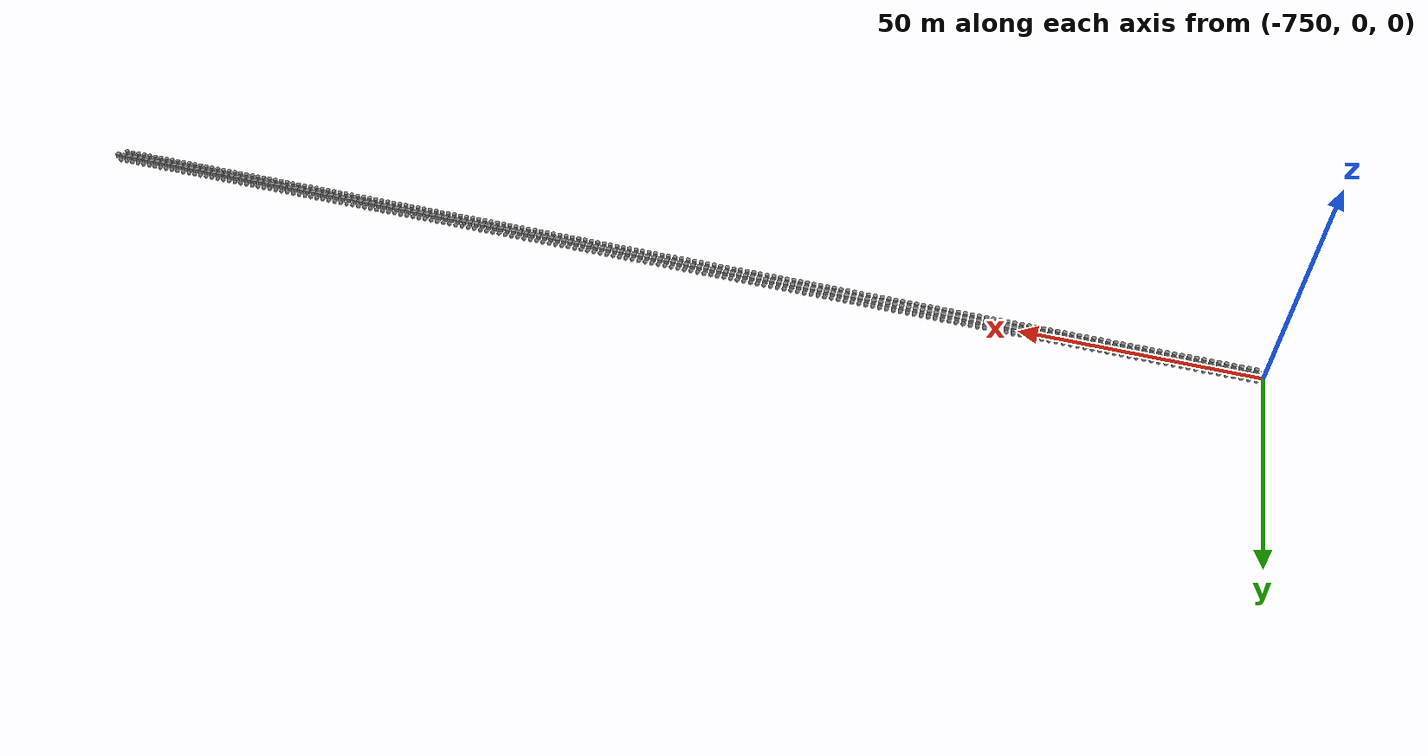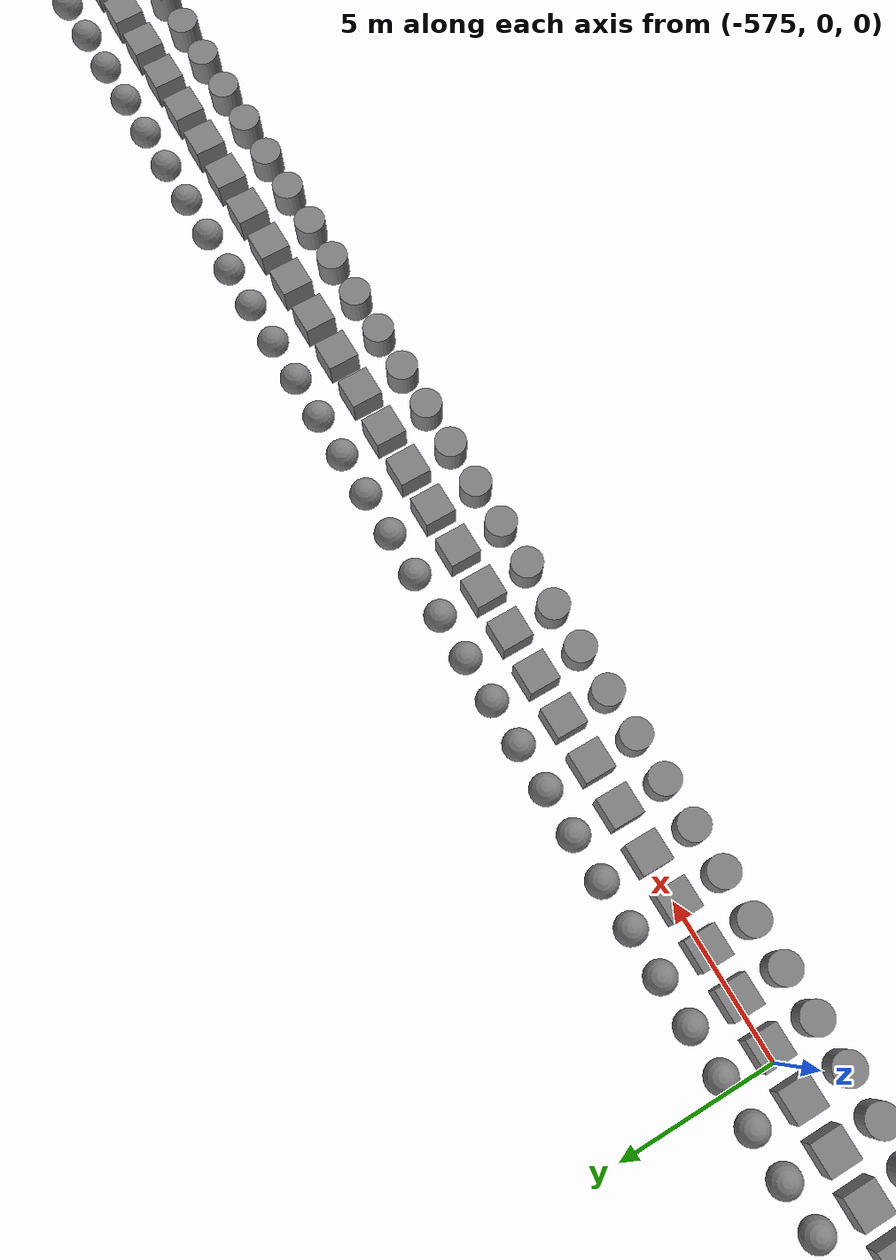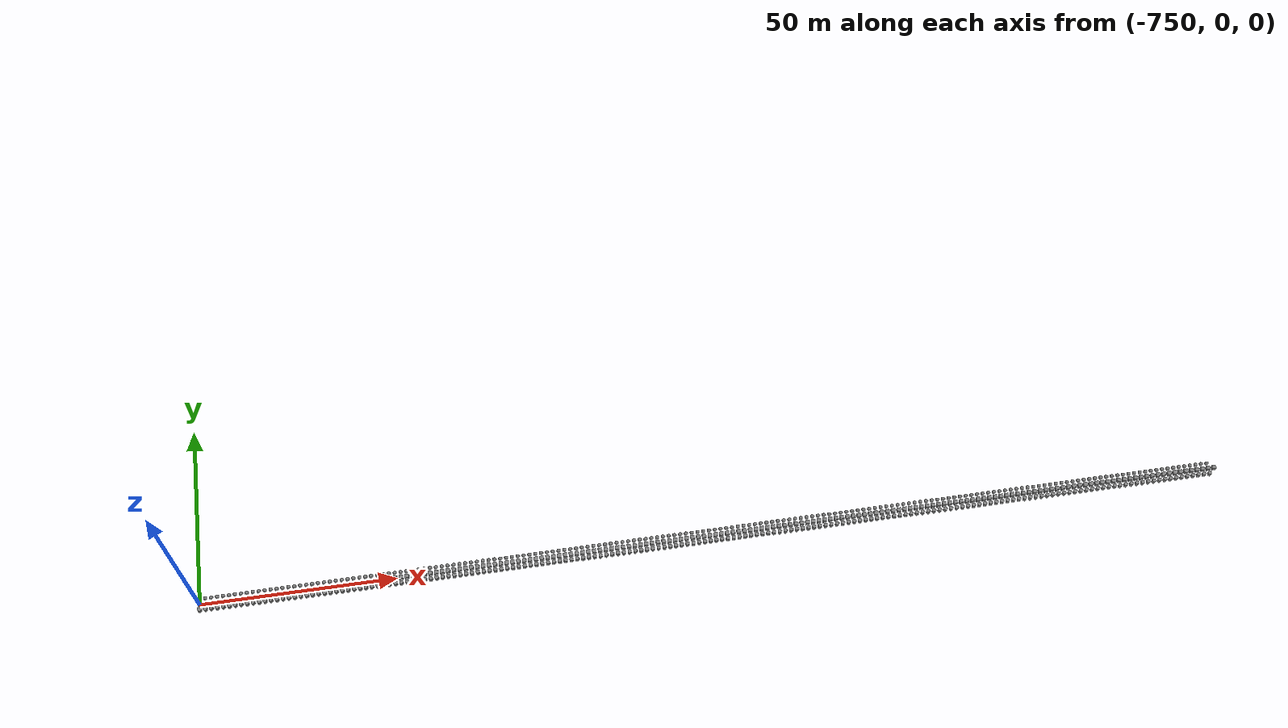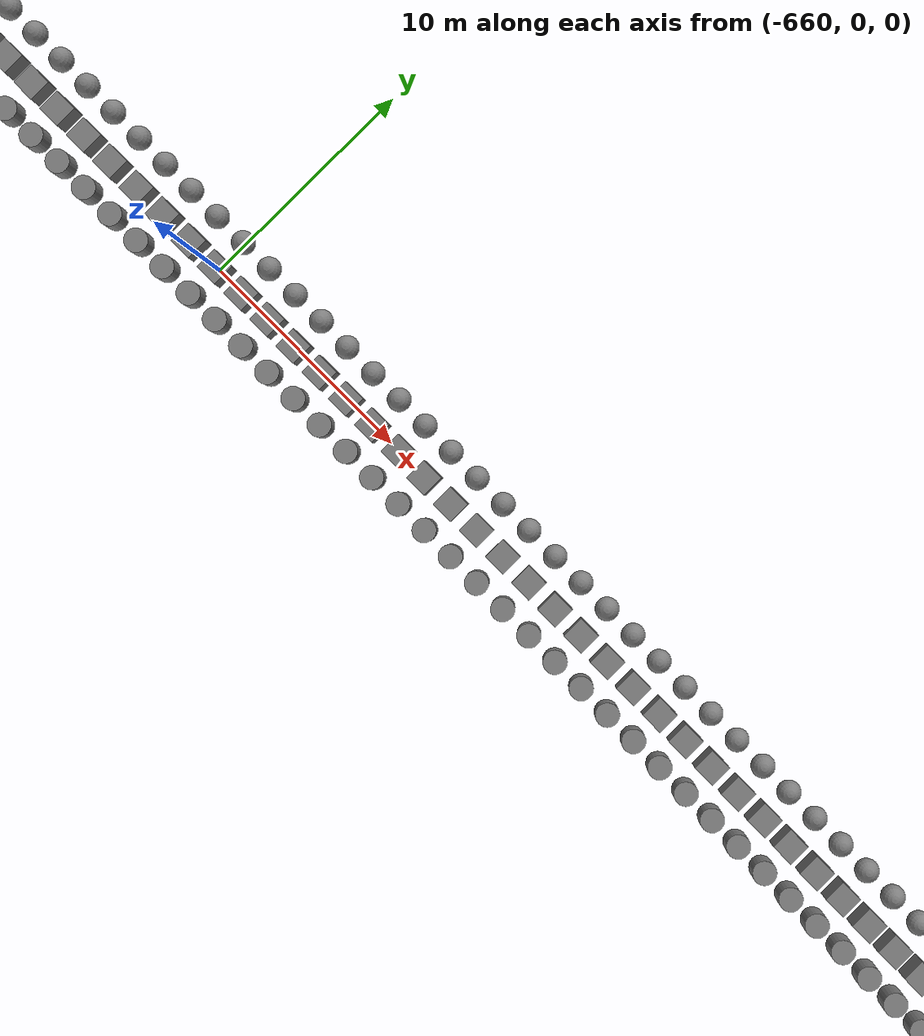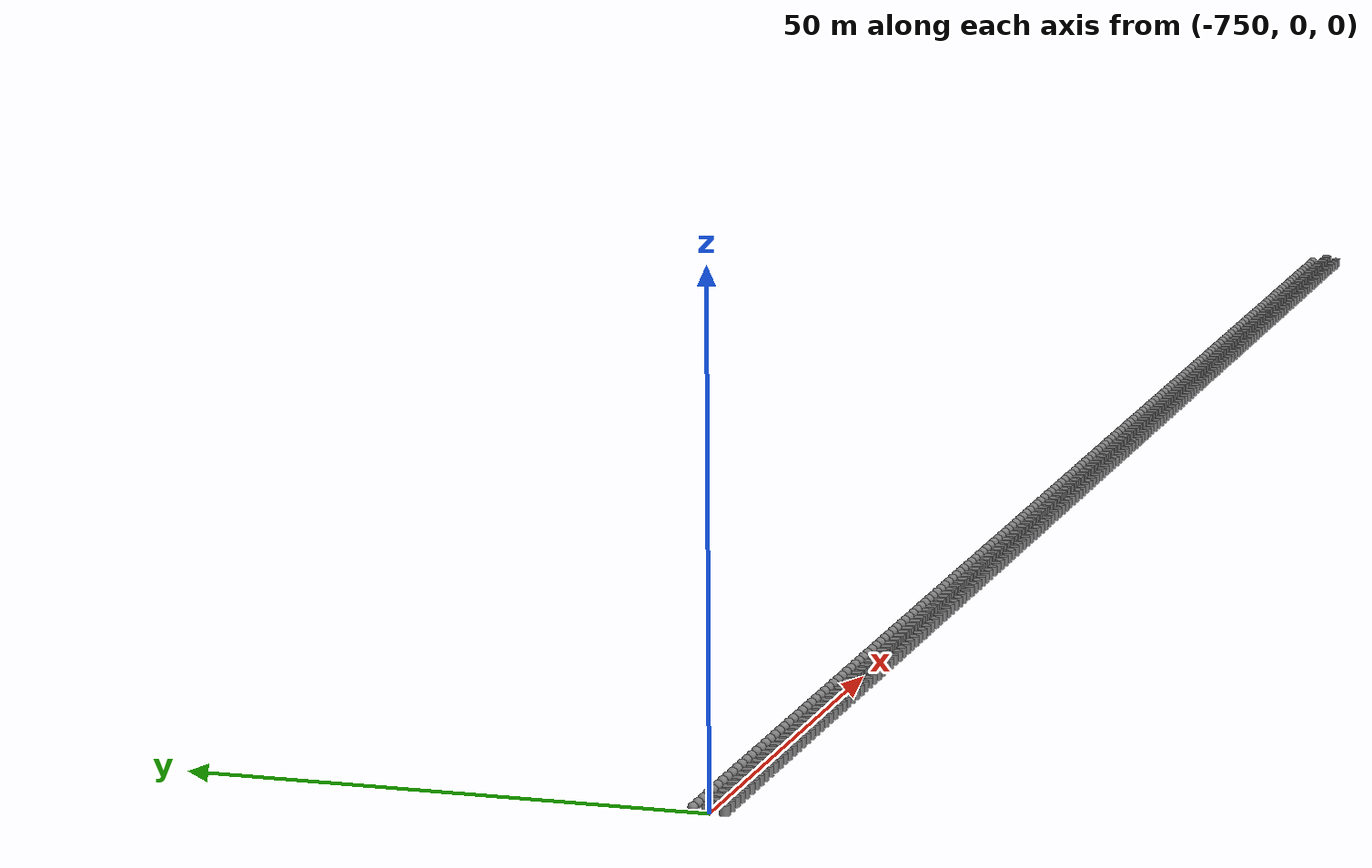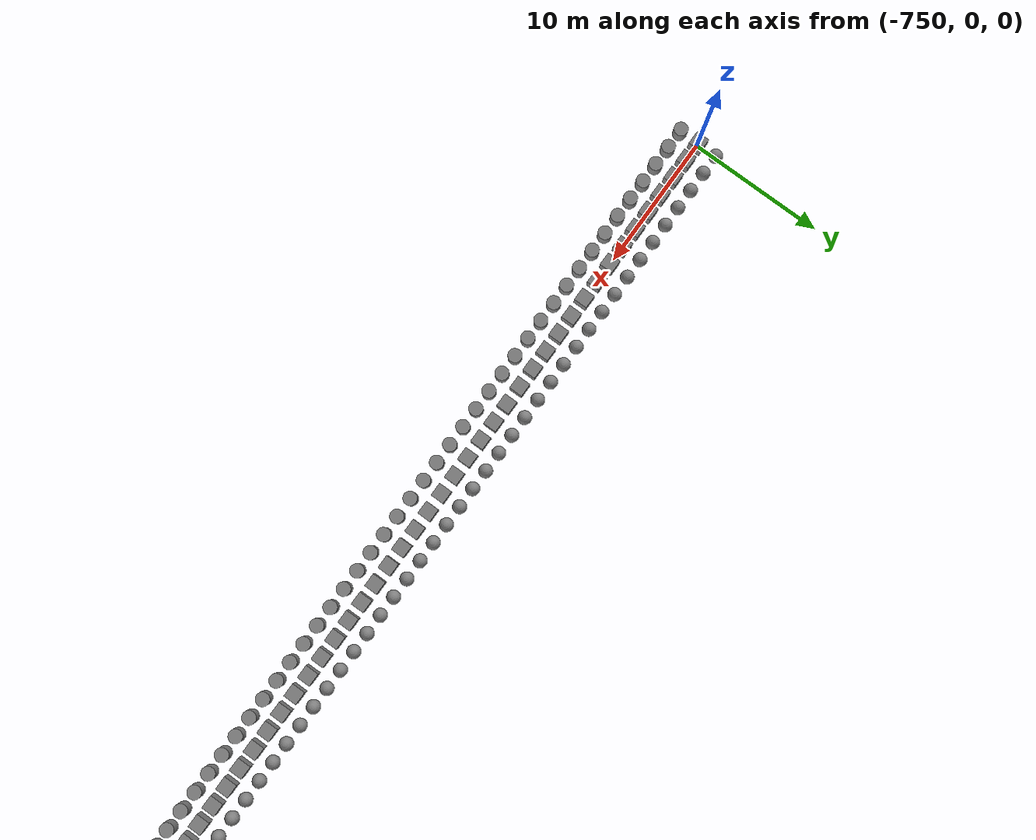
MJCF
<mujoco model="MuJoCo Model">
  <compiler angle="radian"/>

  <option timestep="0.001" gravity="0 0 -9.8">
    <flag sleep="enable"/>
  </option>

  <worldbody>
    <body name="ground_plane::link">
      <inertial pos="0 0 0" mass="1" diaginertia="1 1 1"/>
      <geom name="ground_plane::link::collision" size="50 50 1" type="plane"/>
    </body>
    <body name="box_0::box_link" pos="-750 0 0.5">
      <inertial pos="0 0 0" mass="1" diaginertia="1 1 1"/>
      <joint type="free"/>
      <geom name="box_0::box_link::box_collision" size="0.5 0.5 0.5" type="box"/>
    </body>
    <body name="cylinder_0::cylinder_link" pos="-750 -1.5 0.5">
      <inertial pos="0 0 0" mass="2" diaginertia="2 2 2"/>
      <joint type="free"/>
      <geom name="cylinder_0::cylinder_link::cylinder_collision" size="0.5 0.5" type="cylinder"/>
    </body>
    <body name="sphere_0::sphere_link" pos="-750 1.5 0.5">
      <inertial pos="0 0 0" mass="3" diaginertia="3 3 3"/>
      <joint type="free"/>
      <geom name="sphere_0::sphere_link::sphere_collision" size="0.5"/>
    </body>
    <body name="box_1::box_link" pos="-748.5 0 0.5">
      <inertial pos="0 0 0" mass="1" diaginertia="1 1 1"/>
      <joint type="free"/>
      <geom name="box_1::box_link::box_collision" size="0.5 0.5 0.5" type="box"/>
    </body>
    <body name="cylinder_1::cylinder_link" pos="-748.5 -1.5 0.5">
      <inertial pos="0 0 0" mass="2" diaginertia="2 2 2"/>
      <joint type="free"/>
      <geom name="cylinder_1::cylinder_link::cylinder_collision" size="0.5 0.5" type="cylinder"/>
    </body>
    <body name="sphere_1::sphere_link" pos="-748.5 1.5 0.5">
      <inertial pos="0 0 0" mass="3" diaginertia="3 3 3"/>
      <joint type="free"/>
      <geom name="sphere_1::sphere_link::sphere_collision" size="0.5"/>
    </body>
    <body name="box_2::box_link" pos="-747 0 0.5">
      <inertial pos="0 0 0" mass="1" diaginertia="1 1 1"/>
      <joint type="free"/>
      <geom name="box_2::box_link::box_collision" size="0.5 0.5 0.5" type="box"/>
    </body>
    <body name="cylinder_2::cylinder_link" pos="-747 -1.5 0.5">
      <inertial pos="0 0 0" mass="2" diaginertia="2 2 2"/>
      <joint type="free"/>
      <geom name="cylinder_2::cylinder_link::cylinder_collision" size="0.5 0.5" type="cylinder"/>
    </body>
    <body name="sphere_2::sphere_link" pos="-747 1.5 0.5">
      <inertial pos="0 0 0" mass="3" diaginertia="3 3 3"/>
      <joint type="free"/>
      <geom name="sphere_2::sphere_link::sphere_collision" size="0.5"/>
    </body>
    <body name="box_3::box_link" pos="-745.5 0 0.5">
      <inertial pos="0 0 0" mass="1" diaginertia="1 1 1"/>
      <joint type="free"/>
      <geom name="box_3::box_link::box_collision" size="0.5 0.5 0.5" type="box"/>
    </body>
    <body name="cylinder_3::cylinder_link" pos="-745.5 -1.5 0.5">
      <inertial pos="0 0 0" mass="2" diaginertia="2 2 2"/>
      <joint type="free"/>
      <geom name="cylinder_3::cylinder_link::cylinder_collision" size="0.5 0.5" type="cylinder"/>
    </body>
    <body name="sphere_3::sphere_link" pos="-745.5 1.5 0.5">
      <inertial pos="0 0 0" mass="3" diaginertia="3 3 3"/>
      <joint type="free"/>
      <geom name="sphere_3::sphere_link::sphere_collision" size="0.5"/>
    </body>
    <body name="box_4::box_link" pos="-744 0 0.5">
      <inertial pos="0 0 0" mass="1" diaginertia="1 1 1"/>
      <joint type="free"/>
      <geom name="box_4::box_link::box_collision" size="0.5 0.5 0.5" type="box"/>
    </body>
    <body name="cylinder_4::cylinder_link" pos="-744 -1.5 0.5">
      <inertial pos="0 0 0" mass="2" diaginertia="2 2 2"/>
      <joint type="free"/>
      <geom name="cylinder_4::cylinder_link::cylinder_collision" size="0.5 0.5" type="cylinder"/>
    </body>
    <body name="sphere_4::sphere_link" pos="-744 1.5 0.5">
      <inertial pos="0 0 0" mass="3" diaginertia="3 3 3"/>
      <joint type="free"/>
      <geom name="sphere_4::sphere_link::sphere_collision" size="0.5"/>
    </body>
    <body name="box_5::box_link" pos="-742.5 0 0.5">
      <inertial pos="0 0 0" mass="1" diaginertia="1 1 1"/>
      <joint type="free"/>
      <geom name="box_5::box_link::box_collision" size="0.5 0.5 0.5" type="box"/>
    </body>
    <body name="cylinder_5::cylinder_link" pos="-742.5 -1.5 0.5">
      <inertial pos="0 0 0" mass="2" diaginertia="2 2 2"/>
      <joint type="free"/>
      <geom name="cylinder_5::cylinder_link::cylinder_collision" size="0.5 0.5" type="cylinder"/>
    </body>
    <body name="sphere_5::sphere_link" pos="-742.5 1.5 0.5">
      <inertial pos="0 0 0" mass="3" diaginertia="3 3 3"/>
      <joint type="free"/>
      <geom name="sphere_5::sphere_link::sphere_collision" size="0.5"/>
    </body>
    <body name="box_6::box_link" pos="-741 0 0.5">
      <inertial pos="0 0 0" mass="1" diaginertia="1 1 1"/>
      <joint type="free"/>
      <geom name="box_6::box_link::box_collision" size="0.5 0.5 0.5" type="box"/>
    </body>
    <body name="cylinder_6::cylinder_link" pos="-741 -1.5 0.5">
      <inertial pos="0 0 0" mass="2" diaginertia="2 2 2"/>
      <joint type="free"/>
      <geom name="cylinder_6::cylinder_link::cylinder_collision" size="0.5 0.5" type="cylinder"/>
    </body>
    <body name="sphere_6::sphere_link" pos="-741 1.5 0.5">
      <inertial pos="0 0 0" mass="3" diaginertia="3 3 3"/>
      <joint type="free"/>
      <geom name="sphere_6::sphere_link::sphere_collision" size="0.5"/>
    </body>
    <body name="box_7::box_link" pos="-739.5 0 0.5">
      <inertial pos="0 0 0" mass="1" diaginertia="1 1 1"/>
      <joint type="free"/>
      <geom name="box_7::box_link::box_collision" size="0.5 0.5 0.5" type="box"/>
    </body>
    <body name="cylinder_7::cylinder_link" pos="-739.5 -1.5 0.5">
      <inertial pos="0 0 0" mass="2" diaginertia="2 2 2"/>
      <joint type="free"/>
      <geom name="cylinder_7::cylinder_link::cylinder_collision" size="0.5 0.5" type="cylinder"/>
    </body>
    <body name="sphere_7::sphere_link" pos="-739.5 1.5 0.5">
      <inertial pos="0 0 0" mass="3" diaginertia="3 3 3"/>
      <joint type="free"/>
      <geom name="sphere_7::sphere_link::sphere_collision" size="0.5"/>
    </body>
    <body name="box_8::box_link" pos="-738 0 0.5">
      <inertial pos="0 0 0" mass="1" diaginertia="1 1 1"/>
      <joint type="free"/>
      <geom name="box_8::box_link::box_collision" size="0.5 0.5 0.5" type="box"/>
    </body>
    <body name="cylinder_8::cylinder_link" pos="-738 -1.5 0.5">
      <inertial pos="0 0 0" mass="2" diaginertia="2 2 2"/>
      <joint type="free"/>
      <geom name="cylinder_8::cylinder_link::cylinder_collision" size="0.5 0.5" type="cylinder"/>
    </body>
    <body name="sphere_8::sphere_link" pos="-738 1.5 0.5">
      <inertial pos="0 0 0" mass="3" diaginertia="3 3 3"/>
      <joint type="free"/>
      <geom name="sphere_8::sphere_link::sphere_collision" size="0.5"/>
    </body>
    <body name="box_9::box_link" pos="-736.5 0 0.5">
      <inertial pos="0 0 0" mass="1" diaginertia="1 1 1"/>
      <joint type="free"/>
      <geom name="box_9::box_link::box_collision" size="0.5 0.5 0.5" type="box"/>
    </body>
    <body name="cylinder_9::cylinder_link" pos="-736.5 -1.5 0.5">
      <inertial pos="0 0 0" mass="2" diaginertia="2 2 2"/>
      <joint type="free"/>
      <geom name="cylinder_9::cylinder_link::cylinder_collision" size="0.5 0.5" type="cylinder"/>
    </body>
    <body name="sphere_9::sphere_link" pos="-736.5 1.5 0.5">
      <inertial pos="0 0 0" mass="3" diaginertia="3 3 3"/>
      <joint type="free"/>
      <geom name="sphere_9::sphere_link::sphere_collision" size="0.5"/>
    </body>
    <body name="box_10::box_link" pos="-735 0 0.5">
      <inertial pos="0 0 0" mass="1" diaginertia="1 1 1"/>
      <joint type="free"/>
      <geom name="box_10::box_link::box_collision" size="0.5 0.5 0.5" type="box"/>
    </body>
    <body name="cylinder_10::cylinder_link" pos="-735 -1.5 0.5">
      <inertial pos="0 0 0" mass="2" diaginertia="2 2 2"/>
      <joint type="free"/>
      <geom name="cylinder_10::cylinder_link::cylinder_collision" size="0.5 0.5" type="cylinder"/>
    </body>
    <body name="sphere_10::sphere_link" pos="-735 1.5 0.5">
      <inertial pos="0 0 0" mass="3" diaginertia="3 3 3"/>
      <joint type="free"/>
      <geom name="sphere_10::sphere_link::sphere_collision" size="0.5"/>
    </body>
    <body name="box_11::box_link" pos="-733.5 0 0.5">
      <inertial pos="0 0 0" mass="1" diaginertia="1 1 1"/>
      <joint type="free"/>
      <geom name="box_11::box_link::box_collision" size="0.5 0.5 0.5" type="box"/>
    </body>
    <body name="cylinder_11::cylinder_link" pos="-733.5 -1.5 0.5">
      <inertial pos="0 0 0" mass="2" diaginertia="2 2 2"/>
      <joint type="free"/>
      <geom name="cylinder_11::cylinder_link::cylinder_collision" size="0.5 0.5" type="cylinder"/>
    </body>
    <body name="sphere_11::sphere_link" pos="-733.5 1.5 0.5">
      <inertial pos="0 0 0" mass="3" diaginertia="3 3 3"/>
      <joint type="free"/>
      <geom name="sphere_11::sphere_link::sphere_collision" size="0.5"/>
    </body>
    <body name="box_12::box_link" pos="-732 0 0.5">
      <inertial pos="0 0 0" mass="1" diaginertia="1 1 1"/>
      <joint type="free"/>
      <geom name="box_12::box_link::box_collision" size="0.5 0.5 0.5" type="box"/>
    </body>
    <body name="cylinder_12::cylinder_link" pos="-732 -1.5 0.5">
      <inertial pos="0 0 0" mass="2" diaginertia="2 2 2"/>
      <joint type="free"/>
      <geom name="cylinder_12::cylinder_link::cylinder_collision" size="0.5 0.5" type="cylinder"/>
    </body>
    <body name="sphere_12::sphere_link" pos="-732 1.5 0.5">
      <inertial pos="0 0 0" mass="3" diaginertia="3 3 3"/>
      <joint type="free"/>
      <geom name="sphere_12::sphere_link::sphere_collision" size="0.5"/>
    </body>
    <body name="box_13::box_link" pos="-730.5 0 0.5">
      <inertial pos="0 0 0" mass="1" diaginertia="1 1 1"/>
      <joint type="free"/>
      <geom name="box_13::box_link::box_collision" size="0.5 0.5 0.5" type="box"/>
    </body>
    <body name="cylinder_13::cylinder_link" pos="-730.5 -1.5 0.5">
      <inertial pos="0 0 0" mass="2" diaginertia="2 2 2"/>
      <joint type="free"/>
      <geom name="cylinder_13::cylinder_link::cylinder_collision" size="0.5 0.5" type="cylinder"/>
    </body>
    <body name="sphere_13::sphere_link" pos="-730.5 1.5 0.5">
      <inertial pos="0 0 0" mass="3" diaginertia="3 3 3"/>
      <joint type="free"/>
      <geom name="sphere_13::sphere_link::sphere_collision" size="0.5"/>
    </body>
    <body name="box_14::box_link" pos="-729 0 0.5">
      <inertial pos="0 0 0" mass="1" diaginertia="1 1 1"/>
      <joint type="free"/>
      <geom name="box_14::box_link::box_collision" size="0.5 0.5 0.5" type="box"/>
    </body>
    <body name="cylinder_14::cylinder_link" pos="-729 -1.5 0.5">
      <inertial pos="0 0 0" mass="2" diaginertia="2 2 2"/>
      <joint type="free"/>
      <geom name="cylinder_14::cylinder_link::cylinder_collision" size="0.5 0.5" type="cylinder"/>
    </body>
    <body name="sphere_14::sphere_link" pos="-729 1.5 0.5">
      <inertial pos="0 0 0" mass="3" diaginertia="3 3 3"/>
      <joint type="free"/>
      <geom name="sphere_14::sphere_link::sphere_collision" size="0.5"/>
    </body>
    <body name="box_15::box_link" pos="-727.5 0 0.5">
      <inertial pos="0 0 0" mass="1" diaginertia="1 1 1"/>
      <joint type="free"/>
      <geom name="box_15::box_link::box_collision" size="0.5 0.5 0.5" type="box"/>
    </body>
    <body name="cylinder_15::cylinder_link" pos="-727.5 -1.5 0.5">
      <inertial pos="0 0 0" mass="2" diaginertia="2 2 2"/>
      <joint type="free"/>
      <geom name="cylinder_15::cylinder_link::cylinder_collision" size="0.5 0.5" type="cylinder"/>
    </body>
    <body name="sphere_15::sphere_link" pos="-727.5 1.5 0.5">
      <inertial pos="0 0 0" mass="3" diaginertia="3 3 3"/>
      <joint type="free"/>
      <geom name="sphere_15::sphere_link::sphere_collision" size="0.5"/>
    </body>
    <body name="box_16::box_link" pos="-726 0 0.5">
      <inertial pos="0 0 0" mass="1" diaginertia="1 1 1"/>
      <joint type="free"/>
      <geom name="box_16::box_link::box_collision" size="0.5 0.5 0.5" type="box"/>
    </body>
    <body name="cylinder_16::cylinder_link" pos="-726 -1.5 0.5">
      <inertial pos="0 0 0" mass="2" diaginertia="2 2 2"/>
      <joint type="free"/>
      <geom name="cylinder_16::cylinder_link::cylinder_collision" size="0.5 0.5" type="cylinder"/>
    </body>
    <body name="sphere_16::sphere_link" pos="-726 1.5 0.5">
      <inertial pos="0 0 0" mass="3" diaginertia="3 3 3"/>
      <joint type="free"/>
      <geom name="sphere_16::sphere_link::sphere_collision" size="0.5"/>
    </body>
    <body name="box_17::box_link" pos="-724.5 0 0.5">
      <inertial pos="0 0 0" mass="1" diaginertia="1 1 1"/>
      <joint type="free"/>
      <geom name="box_17::box_link::box_collision" size="0.5 0.5 0.5" type="box"/>
    </body>
    <body name="cylinder_17::cylinder_link" pos="-724.5 -1.5 0.5">
      <inertial pos="0 0 0" mass="2" diaginertia="2 2 2"/>
      <joint type="free"/>
      <geom name="cylinder_17::cylinder_link::cylinder_collision" size="0.5 0.5" type="cylinder"/>
    </body>
    <body name="sphere_17::sphere_link" pos="-724.5 1.5 0.5">
      <inertial pos="0 0 0" mass="3" diaginertia="3 3 3"/>
      <joint type="free"/>
      <geom name="sphere_17::sphere_link::sphere_collision" size="0.5"/>
    </body>
    <body name="box_18::box_link" pos="-723 0 0.5">
      <inertial pos="0 0 0" mass="1" diaginertia="1 1 1"/>
      <joint type="free"/>
      <geom name="box_18::box_link::box_collision" size="0.5 0.5 0.5" type="box"/>
    </body>
    <body name="cylinder_18::cylinder_link" pos="-723 -1.5 0.5">
      <inertial pos="0 0 0" mass="2" diaginertia="2 2 2"/>
      <joint type="free"/>
      <geom name="cylinder_18::cylinder_link::cylinder_collision" size="0.5 0.5" type="cylinder"/>
    </body>
    <body name="sphere_18::sphere_link" pos="-723 1.5 0.5">
      <inertial pos="0 0 0" mass="3" diaginertia="3 3 3"/>
      <joint type="free"/>
      <geom name="sphere_18::sphere_link::sphere_collision" size="0.5"/>
    </body>
    <body name="box_19::box_link" pos="-721.5 0 0.5">
      <inertial pos="0 0 0" mass="1" diaginertia="1 1 1"/>
      <joint type="free"/>
      <geom name="box_19::box_link::box_collision" size="0.5 0.5 0.5" type="box"/>
    </body>
    <body name="cylinder_19::cylinder_link" pos="-721.5 -1.5 0.5">
      <inertial pos="0 0 0" mass="2" diaginertia="2 2 2"/>
      <joint type="free"/>
      <geom name="cylinder_19::cylinder_link::cylinder_collision" size="0.5 0.5" type="cylinder"/>
    </body>
    <body name="sphere_19::sphere_link" pos="-721.5 1.5 0.5">
      <inertial pos="0 0 0" mass="3" diaginertia="3 3 3"/>
      <joint type="free"/>
      <geom name="sphere_19::sphere_link::sphere_collision" size="0.5"/>
    </body>
    <body name="box_20::box_link" pos="-720 0 0.5">
      <inertial pos="0 0 0" mass="1" diaginertia="1 1 1"/>
      <joint type="free"/>
      <geom name="box_20::box_link::box_collision" size="0.5 0.5 0.5" type="box"/>
    </body>
    <body name="cylinder_20::cylinder_link" pos="-720 -1.5 0.5">
      <inertial pos="0 0 0" mass="2" diaginertia="2 2 2"/>
      <joint type="free"/>
      <geom name="cylinder_20::cylinder_link::cylinder_collision" size="0.5 0.5" type="cylinder"/>
    </body>
    <body name="sphere_20::sphere_link" pos="-720 1.5 0.5">
      <inertial pos="0 0 0" mass="3" diaginertia="3 3 3"/>
      <joint type="free"/>
      <geom name="sphere_20::sphere_link::sphere_collision" size="0.5"/>
    </body>
    <body name="box_21::box_link" pos="-718.5 0 0.5">
      <inertial pos="0 0 0" mass="1" diaginertia="1 1 1"/>
      <joint type="free"/>
      <geom name="box_21::box_link::box_collision" size="0.5 0.5 0.5" type="box"/>
    </body>
    <body name="cylinder_21::cylinder_link" pos="-718.5 -1.5 0.5">
      <inertial pos="0 0 0" mass="2" diaginertia="2 2 2"/>
      <joint type="free"/>
      <geom name="cylinder_21::cylinder_link::cylinder_collision" size="0.5 0.5" type="cylinder"/>
    </body>
    <body name="sphere_21::sphere_link" pos="-718.5 1.5 0.5">
      <inertial pos="0 0 0" mass="3" diaginertia="3 3 3"/>
      <joint type="free"/>
      <geom name="sphere_21::sphere_link::sphere_collision" size="0.5"/>
    </body>
    <body name="box_22::box_link" pos="-717 0 0.5">
      <inertial pos="0 0 0" mass="1" diaginertia="1 1 1"/>
      <joint type="free"/>
      <geom name="box_22::box_link::box_collision" size="0.5 0.5 0.5" type="box"/>
    </body>
    <body name="cylinder_22::cylinder_link" pos="-717 -1.5 0.5">
      <inertial pos="0 0 0" mass="2" diaginertia="2 2 2"/>
      <joint type="free"/>
      <geom name="cylinder_22::cylinder_link::cylinder_collision" size="0.5 0.5" type="cylinder"/>
    </body>
    <body name="sphere_22::sphere_link" pos="-717 1.5 0.5">
      <inertial pos="0 0 0" mass="3" diaginertia="3 3 3"/>
      <joint type="free"/>
      <geom name="sphere_22::sphere_link::sphere_collision" size="0.5"/>
    </body>
    <body name="box_23::box_link" pos="-715.5 0 0.5">
      <inertial pos="0 0 0" mass="1" diaginertia="1 1 1"/>
      <joint type="free"/>
      <geom name="box_23::box_link::box_collision" size="0.5 0.5 0.5" type="box"/>
    </body>
    <body name="cylinder_23::cylinder_link" pos="-715.5 -1.5 0.5">
      <inertial pos="0 0 0" mass="2" diaginertia="2 2 2"/>
      <joint type="free"/>
      <geom name="cylinder_23::cylinder_link::cylinder_collision" size="0.5 0.5" type="cylinder"/>
    </body>
    <body name="sphere_23::sphere_link" pos="-715.5 1.5 0.5">
      <inertial pos="0 0 0" mass="3" diaginertia="3 3 3"/>
      <joint type="free"/>
      <geom name="sphere_23::sphere_link::sphere_collision" size="0.5"/>
    </body>
    <body name="box_24::box_link" pos="-714 0 0.5">
      <inertial pos="0 0 0" mass="1" diaginertia="1 1 1"/>
      <joint type="free"/>
      <geom name="box_24::box_link::box_collision" size="0.5 0.5 0.5" type="box"/>
    </body>
    <body name="cylinder_24::cylinder_link" pos="-714 -1.5 0.5">
      <inertial pos="0 0 0" mass="2" diaginertia="2 2 2"/>
      <joint type="free"/>
      <geom name="cylinder_24::cylinder_link::cylinder_collision" size="0.5 0.5" type="cylinder"/>
    </body>
    <body name="sphere_24::sphere_link" pos="-714 1.5 0.5">
      <inertial pos="0 0 0" mass="3" diaginertia="3 3 3"/>
      <joint type="free"/>
      <geom name="sphere_24::sphere_link::sphere_collision" size="0.5"/>
    </body>
    <body name="box_25::box_link" pos="-712.5 0 0.5">
      <inertial pos="0 0 0" mass="1" diaginertia="1 1 1"/>
      <joint type="free"/>
      <geom name="box_25::box_link::box_collision" size="0.5 0.5 0.5" type="box"/>
    </body>
    <body name="cylinder_25::cylinder_link" pos="-712.5 -1.5 0.5">
      <inertial pos="0 0 0" mass="2" diaginertia="2 2 2"/>
      <joint type="free"/>
      <geom name="cylinder_25::cylinder_link::cylinder_collision" size="0.5 0.5" type="cylinder"/>
    </body>
    <body name="sphere_25::sphere_link" pos="-712.5 1.5 0.5">
      <inertial pos="0 0 0" mass="3" diaginertia="3 3 3"/>
      <joint type="free"/>
      <geom name="sphere_25::sphere_link::sphere_collision" size="0.5"/>
    </body>
    <body name="box_26::box_link" pos="-711 0 0.5">
      <inertial pos="0 0 0" mass="1" diaginertia="1 1 1"/>
      <joint type="free"/>
      <geom name="box_26::box_link::box_collision" size="0.5 0.5 0.5" type="box"/>
    </body>
    <body name="cylinder_26::cylinder_link" pos="-711 -1.5 0.5">
      <inertial pos="0 0 0" mass="2" diaginertia="2 2 2"/>
      <joint type="free"/>
      <geom name="cylinder_26::cylinder_link::cylinder_collision" size="0.5 0.5" type="cylinder"/>
    </body>
    <body name="sphere_26::sphere_link" pos="-711 1.5 0.5">
      <inertial pos="0 0 0" mass="3" diaginertia="3 3 3"/>
      <joint type="free"/>
      <geom name="sphere_26::sphere_link::sphere_collision" size="0.5"/>
    </body>
    <body name="box_27::box_link" pos="-709.5 0 0.5">
      <inertial pos="0 0 0" mass="1" diaginertia="1 1 1"/>
      <joint type="free"/>
      <geom name="box_27::box_link::box_collision" size="0.5 0.5 0.5" type="box"/>
    </body>
    <body name="cylinder_27::cylinder_link" pos="-709.5 -1.5 0.5">
      <inertial pos="0 0 0" mass="2" diaginertia="2 2 2"/>
      <joint type="free"/>
      <geom name="cylinder_27::cylinder_link::cylinder_collision" size="0.5 0.5" type="cylinder"/>
    </body>
    <body name="sphere_27::sphere_link" pos="-709.5 1.5 0.5">
      <inertial pos="0 0 0" mass="3" diaginertia="3 3 3"/>
      <joint type="free"/>
      <geom name="sphere_27::sphere_link::sphere_collision" size="0.5"/>
    </body>
    <body name="box_28::box_link" pos="-708 0 0.5">
      <inertial pos="0 0 0" mass="1" diaginertia="1 1 1"/>
      <joint type="free"/>
      <geom name="box_28::box_link::box_collision" size="0.5 0.5 0.5" type="box"/>
    </body>
    <body name="cylinder_28::cylinder_link" pos="-708 -1.5 0.5">
      <inertial pos="0 0 0" mass="2" diaginertia="2 2 2"/>
      <joint type="free"/>
      <geom name="cylinder_28::cylinder_link::cylinder_collision" size="0.5 0.5" type="cylinder"/>
    </body>
    <body name="sphere_28::sphere_link" pos="-708 1.5 0.5">
      <inertial pos="0 0 0" mass="3" diaginertia="3 3 3"/>
      <joint type="free"/>
      <geom name="sphere_28::sphere_link::sphere_collision" size="0.5"/>
    </body>
    <body name="box_29::box_link" pos="-706.5 0 0.5">
      <inertial pos="0 0 0" mass="1" diaginertia="1 1 1"/>
      <joint type="free"/>
      <geom name="box_29::box_link::box_collision" size="0.5 0.5 0.5" type="box"/>
    </body>
    <body name="cylinder_29::cylinder_link" pos="-706.5 -1.5 0.5">
      <inertial pos="0 0 0" mass="2" diaginertia="2 2 2"/>
      <joint type="free"/>
      <geom name="cylinder_29::cylinder_link::cylinder_collision" size="0.5 0.5" type="cylinder"/>
    </body>
    <body name="sphere_29::sphere_link" pos="-706.5 1.5 0.5">
      <inertial pos="0 0 0" mass="3" diaginertia="3 3 3"/>
      <joint type="free"/>
      <geom name="sphere_29::sphere_link::sphere_collision" size="0.5"/>
    </body>
    <body name="box_30::box_link" pos="-705 0 0.5">
      <inertial pos="0 0 0" mass="1" diaginertia="1 1 1"/>
      <joint type="free"/>
      <geom name="box_30::box_link::box_collision" size="0.5 0.5 0.5" type="box"/>
    </body>
    <body name="cylinder_30::cylinder_link" pos="-705 -1.5 0.5">
      <inertial pos="0 0 0" mass="2" diaginertia="2 2 2"/>
      <joint type="free"/>
      <geom name="cylinder_30::cylinder_link::cylinder_collision" size="0.5 0.5" type="cylinder"/>
    </body>
    <body name="sphere_30::sphere_link" pos="-705 1.5 0.5">
      <inertial pos="0 0 0" mass="3" diaginertia="3 3 3"/>
      <joint type="free"/>
      <geom name="sphere_30::sphere_link::sphere_collision" size="0.5"/>
    </body>
    <body name="box_31::box_link" pos="-703.5 0 0.5">
      <inertial pos="0 0 0" mass="1" diaginertia="1 1 1"/>
      <joint type="free"/>
      <geom name="box_31::box_link::box_collision" size="0.5 0.5 0.5" type="box"/>
    </body>
    <body name="cylinder_31::cylinder_link" pos="-703.5 -1.5 0.5">
      <inertial pos="0 0 0" mass="2" diaginertia="2 2 2"/>
      <joint type="free"/>
      <geom name="cylinder_31::cylinder_link::cylinder_collision" size="0.5 0.5" type="cylinder"/>
    </body>
    <body name="sphere_31::sphere_link" pos="-703.5 1.5 0.5">
      <inertial pos="0 0 0" mass="3" diaginertia="3 3 3"/>
      <joint type="free"/>
      <geom name="sphere_31::sphere_link::sphere_collision" size="0.5"/>
    </body>
    <body name="box_32::box_link" pos="-702 0 0.5">
      <inertial pos="0 0 0" mass="1" diaginertia="1 1 1"/>
      <joint type="free"/>
      <geom name="box_32::box_link::box_collision" size="0.5 0.5 0.5" type="box"/>
    </body>
    <body name="cylinder_32::cylinder_link" pos="-702 -1.5 0.5">
      <inertial pos="0 0 0" mass="2" diaginertia="2 2 2"/>
      <joint type="free"/>
      <geom name="cylinder_32::cylinder_link::cylinder_collision" size="0.5 0.5" type="cylinder"/>
    </body>
    <body name="sphere_32::sphere_link" pos="-702 1.5 0.5">
      <inertial pos="0 0 0" mass="3" diaginertia="3 3 3"/>
      <joint type="free"/>
      <geom name="sphere_32::sphere_link::sphere_collision" size="0.5"/>
    </body>
    <body name="box_33::box_link" pos="-700.5 0 0.5">
      <inertial pos="0 0 0" mass="1" diaginertia="1 1 1"/>
      <joint type="free"/>
      <geom name="box_33::box_link::box_collision" size="0.5 0.5 0.5" type="box"/>
    </body>
    <body name="cylinder_33::cylinder_link" pos="-700.5 -1.5 0.5">
      <inertial pos="0 0 0" mass="2" diaginertia="2 2 2"/>
      <joint type="free"/>
      <geom name="cylinder_33::cylinder_link::cylinder_collision" size="0.5 0.5" type="cylinder"/>
    </body>
    <body name="sphere_33::sphere_link" pos="-700.5 1.5 0.5">
      <inertial pos="0 0 0" mass="3" diaginertia="3 3 3"/>
      <joint type="free"/>
      <geom name="sphere_33::sphere_link::sphere_collision" size="0.5"/>
    </body>
    <body name="box_34::box_link" pos="-699 0 0.5">
      <inertial pos="0 0 0" mass="1" diaginertia="1 1 1"/>
      <joint type="free"/>
      <geom name="box_34::box_link::box_collision" size="0.5 0.5 0.5" type="box"/>
    </body>
    <body name="cylinder_34::cylinder_link" pos="-699 -1.5 0.5">
      <inertial pos="0 0 0" mass="2" diaginertia="2 2 2"/>
      <joint type="free"/>
      <geom name="cylinder_34::cylinder_link::cylinder_collision" size="0.5 0.5" type="cylinder"/>
    </body>
    <body name="sphere_34::sphere_link" pos="-699 1.5 0.5">
      <inertial pos="0 0 0" mass="3" diaginertia="3 3 3"/>
      <joint type="free"/>
      <geom name="sphere_34::sphere_link::sphere_collision" size="0.5"/>
    </body>
    <body name="box_35::box_link" pos="-697.5 0 0.5">
      <inertial pos="0 0 0" mass="1" diaginertia="1 1 1"/>
      <joint type="free"/>
      <geom name="box_35::box_link::box_collision" size="0.5 0.5 0.5" type="box"/>
    </body>
    <body name="cylinder_35::cylinder_link" pos="-697.5 -1.5 0.5">
      <inertial pos="0 0 0" mass="2" diaginertia="2 2 2"/>
      <joint type="free"/>
      <geom name="cylinder_35::cylinder_link::cylinder_collision" size="0.5 0.5" type="cylinder"/>
    </body>
    <body name="sphere_35::sphere_link" pos="-697.5 1.5 0.5">
      <inertial pos="0 0 0" mass="3" diaginertia="3 3 3"/>
      <joint type="free"/>
      <geom name="sphere_35::sphere_link::sphere_collision" size="0.5"/>
    </body>
    <body name="box_36::box_link" pos="-696 0 0.5">
      <inertial pos="0 0 0" mass="1" diaginertia="1 1 1"/>
      <joint type="free"/>
      <geom name="box_36::box_link::box_collision" size="0.5 0.5 0.5" type="box"/>
    </body>
    <body name="cylinder_36::cylinder_link" pos="-696 -1.5 0.5">
      <inertial pos="0 0 0" mass="2" diaginertia="2 2 2"/>
      <joint type="free"/>
      <geom name="cylinder_36::cylinder_link::cylinder_collision" size="0.5 0.5" type="cylinder"/>
    </body>
    <body name="sphere_36::sphere_link" pos="-696 1.5 0.5">
      <inertial pos="0 0 0" mass="3" diaginertia="3 3 3"/>
      <joint type="free"/>
      <geom name="sphere_36::sphere_link::sphere_collision" size="0.5"/>
    </body>
    <body name="box_37::box_link" pos="-694.5 0 0.5">
      <inertial pos="0 0 0" mass="1" diaginertia="1 1 1"/>
      <joint type="free"/>
      <geom name="box_37::box_link::box_collision" size="0.5 0.5 0.5" type="box"/>
    </body>
    <body name="cylinder_37::cylinder_link" pos="-694.5 -1.5 0.5">
      <inertial pos="0 0 0" mass="2" diaginertia="2 2 2"/>
      <joint type="free"/>
      <geom name="cylinder_37::cylinder_link::cylinder_collision" size="0.5 0.5" type="cylinder"/>
    </body>
    <body name="sphere_37::sphere_link" pos="-694.5 1.5 0.5">
      <inertial pos="0 0 0" mass="3" diaginertia="3 3 3"/>
      <joint type="free"/>
      <geom name="sphere_37::sphere_link::sphere_collision" size="0.5"/>
    </body>
    <body name="box_38::box_link" pos="-693 0 0.5">
      <inertial pos="0 0 0" mass="1" diaginertia="1 1 1"/>
      <joint type="free"/>
      <geom name="box_38::box_link::box_collision" size="0.5 0.5 0.5" type="box"/>
    </body>
    <body name="cylinder_38::cylinder_link" pos="-693 -1.5 0.5">
      <inertial pos="0 0 0" mass="2" diaginertia="2 2 2"/>
      <joint type="free"/>
      <geom name="cylinder_38::cylinder_link::cylinder_collision" size="0.5 0.5" type="cylinder"/>
    </body>
    <body name="sphere_38::sphere_link" pos="-693 1.5 0.5">
      <inertial pos="0 0 0" mass="3" diaginertia="3 3 3"/>
      <joint type="free"/>
      <geom name="sphere_38::sphere_link::sphere_collision" size="0.5"/>
    </body>
    <body name="box_39::box_link" pos="-691.5 0 0.5">
      <inertial pos="0 0 0" mass="1" diaginertia="1 1 1"/>
      <joint type="free"/>
      <geom name="box_39::box_link::box_collision" size="0.5 0.5 0.5" type="box"/>
    </body>
    <body name="cylinder_39::cylinder_link" pos="-691.5 -1.5 0.5">
      <inertial pos="0 0 0" mass="2" diaginertia="2 2 2"/>
      <joint type="free"/>
      <geom name="cylinder_39::cylinder_link::cylinder_collision" size="0.5 0.5" type="cylinder"/>
    </body>
    <body name="sphere_39::sphere_link" pos="-691.5 1.5 0.5">
      <inertial pos="0 0 0" mass="3" diaginertia="3 3 3"/>
      <joint type="free"/>
      <geom name="sphere_39::sphere_link::sphere_collision" size="0.5"/>
    </body>
    <body name="box_40::box_link" pos="-690 0 0.5">
      <inertial pos="0 0 0" mass="1" diaginertia="1 1 1"/>
      <joint type="free"/>
      <geom name="box_40::box_link::box_collision" size="0.5 0.5 0.5" type="box"/>
    </body>
    <body name="cylinder_40::cylinder_link" pos="-690 -1.5 0.5">
      <inertial pos="0 0 0" mass="2" diaginertia="2 2 2"/>
      <joint type="free"/>
      <geom name="cylinder_40::cylinder_link::cylinder_collision" size="0.5 0.5" type="cylinder"/>
    </body>
    <body name="sphere_40::sphere_link" pos="-690 1.5 0.5">
      <inertial pos="0 0 0" mass="3" diaginertia="3 3 3"/>
      <joint type="free"/>
      <geom name="sphere_40::sphere_link::sphere_collision" size="0.5"/>
    </body>
    <body name="box_41::box_link" pos="-688.5 0 0.5">
      <inertial pos="0 0 0" mass="1" diaginertia="1 1 1"/>
      <joint type="free"/>
      <geom name="box_41::box_link::box_collision" size="0.5 0.5 0.5" type="box"/>
    </body>
    <body name="cylinder_41::cylinder_link" pos="-688.5 -1.5 0.5">
      <inertial pos="0 0 0" mass="2" diaginertia="2 2 2"/>
      <joint type="free"/>
      <geom name="cylinder_41::cylinder_link::cylinder_collision" size="0.5 0.5" type="cylinder"/>
    </body>
    <body name="sphere_41::sphere_link" pos="-688.5 1.5 0.5">
      <inertial pos="0 0 0" mass="3" diaginertia="3 3 3"/>
      <joint type="free"/>
      <geom name="sphere_41::sphere_link::sphere_collision" size="0.5"/>
    </body>
    <body name="box_42::box_link" pos="-687 0 0.5">
      <inertial pos="0 0 0" mass="1" diaginertia="1 1 1"/>
      <joint type="free"/>
      <geom name="box_42::box_link::box_collision" size="0.5 0.5 0.5" type="box"/>
    </body>
    <body name="cylinder_42::cylinder_link" pos="-687 -1.5 0.5">
      <inertial pos="0 0 0" mass="2" diaginertia="2 2 2"/>
      <joint type="free"/>
      <geom name="cylinder_42::cylinder_link::cylinder_collision" size="0.5 0.5" type="cylinder"/>
    </body>
    <body name="sphere_42::sphere_link" pos="-687 1.5 0.5">
      <inertial pos="0 0 0" mass="3" diaginertia="3 3 3"/>
      <joint type="free"/>
      <geom name="sphere_42::sphere_link::sphere_collision" size="0.5"/>
    </body>
    <body name="box_43::box_link" pos="-685.5 0 0.5">
      <inertial pos="0 0 0" mass="1" diaginertia="1 1 1"/>
      <joint type="free"/>
      <geom name="box_43::box_link::box_collision" size="0.5 0.5 0.5" type="box"/>
    </body>
    <body name="cylinder_43::cylinder_link" pos="-685.5 -1.5 0.5">
      <inertial pos="0 0 0" mass="2" diaginertia="2 2 2"/>
      <joint type="free"/>
      <geom name="cylinder_43::cylinder_link::cylinder_collision" size="0.5 0.5" type="cylinder"/>
    </body>
    <body name="sphere_43::sphere_link" pos="-685.5 1.5 0.5">
      <inertial pos="0 0 0" mass="3" diaginertia="3 3 3"/>
      <joint type="free"/>
      <geom name="sphere_43::sphere_link::sphere_collision" size="0.5"/>
    </body>
    <body name="box_44::box_link" pos="-684 0 0.5">
      <inertial pos="0 0 0" mass="1" diaginertia="1 1 1"/>
      <joint type="free"/>
      <geom name="box_44::box_link::box_collision" size="0.5 0.5 0.5" type="box"/>
    </body>
    <body name="cylinder_44::cylinder_link" pos="-684 -1.5 0.5">
      <inertial pos="0 0 0" mass="2" diaginertia="2 2 2"/>
      <joint type="free"/>
      <geom name="cylinder_44::cylinder_link::cylinder_collision" size="0.5 0.5" type="cylinder"/>
    </body>
    <body name="sphere_44::sphere_link" pos="-684 1.5 0.5">
      <inertial pos="0 0 0" mass="3" diaginertia="3 3 3"/>
      <joint type="free"/>
      <geom name="sphere_44::sphere_link::sphere_collision" size="0.5"/>
    </body>
    <body name="box_45::box_link" pos="-682.5 0 0.5">
      <inertial pos="0 0 0" mass="1" diaginertia="1 1 1"/>
      <joint type="free"/>
      <geom name="box_45::box_link::box_collision" size="0.5 0.5 0.5" type="box"/>
    </body>
    <body name="cylinder_45::cylinder_link" pos="-682.5 -1.5 0.5">
      <inertial pos="0 0 0" mass="2" diaginertia="2 2 2"/>
      <joint type="free"/>
      <geom name="cylinder_45::cylinder_link::cylinder_collision" size="0.5 0.5" type="cylinder"/>
    </body>
    <body name="sphere_45::sphere_link" pos="-682.5 1.5 0.5">
      <inertial pos="0 0 0" mass="3" diaginertia="3 3 3"/>
      <joint type="free"/>
      <geom name="sphere_45::sphere_link::sphere_collision" size="0.5"/>
    </body>
    <body name="box_46::box_link" pos="-681 0 0.5">
      <inertial pos="0 0 0" mass="1" diaginertia="1 1 1"/>
      <joint type="free"/>
      <geom name="box_46::box_link::box_collision" size="0.5 0.5 0.5" type="box"/>
    </body>
    <body name="cylinder_46::cylinder_link" pos="-681 -1.5 0.5">
      <inertial pos="0 0 0" mass="2" diaginertia="2 2 2"/>
      <joint type="free"/>
      <geom name="cylinder_46::cylinder_link::cylinder_collision" size="0.5 0.5" type="cylinder"/>
    </body>
    <body name="sphere_46::sphere_link" pos="-681 1.5 0.5">
      <inertial pos="0 0 0" mass="3" diaginertia="3 3 3"/>
      <joint type="free"/>
      <geom name="sphere_46::sphere_link::sphere_collision" size="0.5"/>
    </body>
    <body name="box_47::box_link" pos="-679.5 0 0.5">
      <inertial pos="0 0 0" mass="1" diaginertia="1 1 1"/>
      <joint type="free"/>
      <geom name="box_47::box_link::box_collision" size="0.5 0.5 0.5" type="box"/>
    </body>
    <body name="cylinder_47::cylinder_link" pos="-679.5 -1.5 0.5">
      <inertial pos="0 0 0" mass="2" diaginertia="2 2 2"/>
      <joint type="free"/>
      <geom name="cylinder_47::cylinder_link::cylinder_collision" size="0.5 0.5" type="cylinder"/>
    </body>
    <body name="sphere_47::sphere_link" pos="-679.5 1.5 0.5">
      <inertial pos="0 0 0" mass="3" diaginertia="3 3 3"/>
      <joint type="free"/>
      <geom name="sphere_47::sphere_link::sphere_collision" size="0.5"/>
    </body>
    <body name="box_48::box_link" pos="-678 0 0.5">
      <inertial pos="0 0 0" mass="1" diaginertia="1 1 1"/>
      <joint type="free"/>
      <geom name="box_48::box_link::box_collision" size="0.5 0.5 0.5" type="box"/>
    </body>
    <body name="cylinder_48::cylinder_link" pos="-678 -1.5 0.5">
      <inertial pos="0 0 0" mass="2" diaginertia="2 2 2"/>
      <joint type="free"/>
      <geom name="cylinder_48::cylinder_link::cylinder_collision" size="0.5 0.5" type="cylinder"/>
    </body>
    <body name="sphere_48::sphere_link" pos="-678 1.5 0.5">
      <inertial pos="0 0 0" mass="3" diaginertia="3 3 3"/>
      <joint type="free"/>
      <geom name="sphere_48::sphere_link::sphere_collision" size="0.5"/>
    </body>
    <body name="box_49::box_link" pos="-676.5 0 0.5">
      <inertial pos="0 0 0" mass="1" diaginertia="1 1 1"/>
      <joint type="free"/>
      <geom name="box_49::box_link::box_collision" size="0.5 0.5 0.5" type="box"/>
    </body>
    <body name="cylinder_49::cylinder_link" pos="-676.5 -1.5 0.5">
      <inertial pos="0 0 0" mass="2" diaginertia="2 2 2"/>
      <joint type="free"/>
      <geom name="cylinder_49::cylinder_link::cylinder_collision" size="0.5 0.5" type="cylinder"/>
    </body>
    <body name="sphere_49::sphere_link" pos="-676.5 1.5 0.5">
      <inertial pos="0 0 0" mass="3" diaginertia="3 3 3"/>
      <joint type="free"/>
      <geom name="sphere_49::sphere_link::sphere_collision" size="0.5"/>
    </body>
    <body name="box_50::box_link" pos="-675 0 0.5">
      <inertial pos="0 0 0" mass="1" diaginertia="1 1 1"/>
      <joint type="free"/>
      <geom name="box_50::box_link::box_collision" size="0.5 0.5 0.5" type="box"/>
    </body>
    <body name="cylinder_50::cylinder_link" pos="-675 -1.5 0.5">
      <inertial pos="0 0 0" mass="2" diaginertia="2 2 2"/>
      <joint type="free"/>
      <geom name="cylinder_50::cylinder_link::cylinder_collision" size="0.5 0.5" type="cylinder"/>
    </body>
    <body name="sphere_50::sphere_link" pos="-675 1.5 0.5">
      <inertial pos="0 0 0" mass="3" diaginertia="3 3 3"/>
      <joint type="free"/>
      <geom name="sphere_50::sphere_link::sphere_collision" size="0.5"/>
    </body>
    <body name="box_51::box_link" pos="-673.5 0 0.5">
      <inertial pos="0 0 0" mass="1" diaginertia="1 1 1"/>
      <joint type="free"/>
      <geom name="box_51::box_link::box_collision" size="0.5 0.5 0.5" type="box"/>
    </body>
    <body name="cylinder_51::cylinder_link" pos="-673.5 -1.5 0.5">
      <inertial pos="0 0 0" mass="2" diaginertia="2 2 2"/>
      <joint type="free"/>
      <geom name="cylinder_51::cylinder_link::cylinder_collision" size="0.5 0.5" type="cylinder"/>
    </body>
    <body name="sphere_51::sphere_link" pos="-673.5 1.5 0.5">
      <inertial pos="0 0 0" mass="3" diaginertia="3 3 3"/>
      <joint type="free"/>
      <geom name="sphere_51::sphere_link::sphere_collision" size="0.5"/>
    </body>
    <body name="box_52::box_link" pos="-672 0 0.5">
      <inertial pos="0 0 0" mass="1" diaginertia="1 1 1"/>
      <joint type="free"/>
      <geom name="box_52::box_link::box_collision" size="0.5 0.5 0.5" type="box"/>
    </body>
    <body name="cylinder_52::cylinder_link" pos="-672 -1.5 0.5">
      <inertial pos="0 0 0" mass="2" diaginertia="2 2 2"/>
      <joint type="free"/>
      <geom name="cylinder_52::cylinder_link::cylinder_collision" size="0.5 0.5" type="cylinder"/>
    </body>
    <body name="sphere_52::sphere_link" pos="-672 1.5 0.5">
      <inertial pos="0 0 0" mass="3" diaginertia="3 3 3"/>
      <joint type="free"/>
      <geom name="sphere_52::sphere_link::sphere_collision" size="0.5"/>
    </body>
    <body name="box_53::box_link" pos="-670.5 0 0.5">
      <inertial pos="0 0 0" mass="1" diaginertia="1 1 1"/>
      <joint type="free"/>
      <geom name="box_53::box_link::box_collision" size="0.5 0.5 0.5" type="box"/>
    </body>
    <body name="cylinder_53::cylinder_link" pos="-670.5 -1.5 0.5">
      <inertial pos="0 0 0" mass="2" diaginertia="2 2 2"/>
      <joint type="free"/>
      <geom name="cylinder_53::cylinder_link::cylinder_collision" size="0.5 0.5" type="cylinder"/>
    </body>
    <body name="sphere_53::sphere_link" pos="-670.5 1.5 0.5">
      <inertial pos="0 0 0" mass="3" diaginertia="3 3 3"/>
      <joint type="free"/>
      <geom name="sphere_53::sphere_link::sphere_collision" size="0.5"/>
    </body>
    <body name="box_54::box_link" pos="-669 0 0.5">
      <inertial pos="0 0 0" mass="1" diaginertia="1 1 1"/>
      <joint type="free"/>
      <geom name="box_54::box_link::box_collision" size="0.5 0.5 0.5" type="box"/>
    </body>
    <body name="cylinder_54::cylinder_link" pos="-669 -1.5 0.5">
      <inertial pos="0 0 0" mass="2" diaginertia="2 2 2"/>
      <joint type="free"/>
      <geom name="cylinder_54::cylinder_link::cylinder_collision" size="0.5 0.5" type="cylinder"/>
    </body>
    <body name="sphere_54::sphere_link" pos="-669 1.5 0.5">
      <inertial pos="0 0 0" mass="3" diaginertia="3 3 3"/>
      <joint type="free"/>
      <geom name="sphere_54::sphere_link::sphere_collision" size="0.5"/>
    </body>
    <body name="box_55::box_link" pos="-667.5 0 0.5">
      <inertial pos="0 0 0" mass="1" diaginertia="1 1 1"/>
      <joint type="free"/>
      <geom name="box_55::box_link::box_collision" size="0.5 0.5 0.5" type="box"/>
    </body>
    <body name="cylinder_55::cylinder_link" pos="-667.5 -1.5 0.5">
      <inertial pos="0 0 0" mass="2" diaginertia="2 2 2"/>
      <joint type="free"/>
      <geom name="cylinder_55::cylinder_link::cylinder_collision" size="0.5 0.5" type="cylinder"/>
    </body>
    <body name="sphere_55::sphere_link" pos="-667.5 1.5 0.5">
      <inertial pos="0 0 0" mass="3" diaginertia="3 3 3"/>
      <joint type="free"/>
      <geom name="sphere_55::sphere_link::sphere_collision" size="0.5"/>
    </body>
    <body name="box_56::box_link" pos="-666 0 0.5">
      <inertial pos="0 0 0" mass="1" diaginertia="1 1 1"/>
      <joint type="free"/>
      <geom name="box_56::box_link::box_collision" size="0.5 0.5 0.5" type="box"/>
    </body>
    <body name="cylinder_56::cylinder_link" pos="-666 -1.5 0.5">
      <inertial pos="0 0 0" mass="2" diaginertia="2 2 2"/>
      <joint type="free"/>
      <geom name="cylinder_56::cylinder_link::cylinder_collision" size="0.5 0.5" type="cylinder"/>
    </body>
    <body name="sphere_56::sphere_link" pos="-666 1.5 0.5">
      <inertial pos="0 0 0" mass="3" diaginertia="3 3 3"/>
      <joint type="free"/>
      <geom name="sphere_56::sphere_link::sphere_collision" size="0.5"/>
    </body>
    <body name="box_57::box_link" pos="-664.5 0 0.5">
      <inertial pos="0 0 0" mass="1" diaginertia="1 1 1"/>
      <joint type="free"/>
      <geom name="box_57::box_link::box_collision" size="0.5 0.5 0.5" type="box"/>
    </body>
    <body name="cylinder_57::cylinder_link" pos="-664.5 -1.5 0.5">
      <inertial pos="0 0 0" mass="2" diaginertia="2 2 2"/>
      <joint type="free"/>
      <geom name="cylinder_57::cylinder_link::cylinder_collision" size="0.5 0.5" type="cylinder"/>
    </body>
    <body name="sphere_57::sphere_link" pos="-664.5 1.5 0.5">
      <inertial pos="0 0 0" mass="3" diaginertia="3 3 3"/>
      <joint type="free"/>
      <geom name="sphere_57::sphere_link::sphere_collision" size="0.5"/>
    </body>
    <body name="box_58::box_link" pos="-663 0 0.5">
      <inertial pos="0 0 0" mass="1" diaginertia="1 1 1"/>
      <joint type="free"/>
      <geom name="box_58::box_link::box_collision" size="0.5 0.5 0.5" type="box"/>
    </body>
    <body name="cylinder_58::cylinder_link" pos="-663 -1.5 0.5">
      <inertial pos="0 0 0" mass="2" diaginertia="2 2 2"/>
      <joint type="free"/>
      <geom name="cylinder_58::cylinder_link::cylinder_collision" size="0.5 0.5" type="cylinder"/>
    </body>
    <body name="sphere_58::sphere_link" pos="-663 1.5 0.5">
      <inertial pos="0 0 0" mass="3" diaginertia="3 3 3"/>
      <joint type="free"/>
      <geom name="sphere_58::sphere_link::sphere_collision" size="0.5"/>
    </body>
    <body name="box_59::box_link" pos="-661.5 0 0.5">
      <inertial pos="0 0 0" mass="1" diaginertia="1 1 1"/>
      <joint type="free"/>
      <geom name="box_59::box_link::box_collision" size="0.5 0.5 0.5" type="box"/>
    </body>
    <body name="cylinder_59::cylinder_link" pos="-661.5 -1.5 0.5">
      <inertial pos="0 0 0" mass="2" diaginertia="2 2 2"/>
      <joint type="free"/>
      <geom name="cylinder_59::cylinder_link::cylinder_collision" size="0.5 0.5" type="cylinder"/>
    </body>
    <body name="sphere_59::sphere_link" pos="-661.5 1.5 0.5">
      <inertial pos="0 0 0" mass="3" diaginertia="3 3 3"/>
      <joint type="free"/>
      <geom name="sphere_59::sphere_link::sphere_collision" size="0.5"/>
    </body>
    <body name="box_60::box_link" pos="-660 0 0.5">
      <inertial pos="0 0 0" mass="1" diaginertia="1 1 1"/>
      <joint type="free"/>
      <geom name="box_60::box_link::box_collision" size="0.5 0.5 0.5" type="box"/>
    </body>
    <body name="cylinder_60::cylinder_link" pos="-660 -1.5 0.5">
      <inertial pos="0 0 0" mass="2" diaginertia="2 2 2"/>
      <joint type="free"/>
      <geom name="cylinder_60::cylinder_link::cylinder_collision" size="0.5 0.5" type="cylinder"/>
    </body>
    <body name="sphere_60::sphere_link" pos="-660 1.5 0.5">
      <inertial pos="0 0 0" mass="3" diaginertia="3 3 3"/>
      <joint type="free"/>
      <geom name="sphere_60::sphere_link::sphere_collision" size="0.5"/>
    </body>
    <body name="box_61::box_link" pos="-658.5 0 0.5">
      <inertial pos="0 0 0" mass="1" diaginertia="1 1 1"/>
      <joint type="free"/>
      <geom name="box_61::box_link::box_collision" size="0.5 0.5 0.5" type="box"/>
    </body>
    <body name="cylinder_61::cylinder_link" pos="-658.5 -1.5 0.5">
      <inertial pos="0 0 0" mass="2" diaginertia="2 2 2"/>
      <joint type="free"/>
      <geom name="cylinder_61::cylinder_link::cylinder_collision" size="0.5 0.5" type="cylinder"/>
    </body>
    <body name="sphere_61::sphere_link" pos="-658.5 1.5 0.5">
      <inertial pos="0 0 0" mass="3" diaginertia="3 3 3"/>
      <joint type="free"/>
      <geom name="sphere_61::sphere_link::sphere_collision" size="0.5"/>
    </body>
    <body name="box_62::box_link" pos="-657 0 0.5">
      <inertial pos="0 0 0" mass="1" diaginertia="1 1 1"/>
      <joint type="free"/>
      <geom name="box_62::box_link::box_collision" size="0.5 0.5 0.5" type="box"/>
    </body>
    <body name="cylinder_62::cylinder_link" pos="-657 -1.5 0.5">
      <inertial pos="0 0 0" mass="2" diaginertia="2 2 2"/>
      <joint type="free"/>
      <geom name="cylinder_62::cylinder_link::cylinder_collision" size="0.5 0.5" type="cylinder"/>
    </body>
    <body name="sphere_62::sphere_link" pos="-657 1.5 0.5">
      <inertial pos="0 0 0" mass="3" diaginertia="3 3 3"/>
      <joint type="free"/>
      <geom name="sphere_62::sphere_link::sphere_collision" size="0.5"/>
    </body>
    <body name="box_63::box_link" pos="-655.5 0 0.5">
      <inertial pos="0 0 0" mass="1" diaginertia="1 1 1"/>
      <joint type="free"/>
      <geom name="box_63::box_link::box_collision" size="0.5 0.5 0.5" type="box"/>
    </body>
    <body name="cylinder_63::cylinder_link" pos="-655.5 -1.5 0.5">
      <inertial pos="0 0 0" mass="2" diaginertia="2 2 2"/>
      <joint type="free"/>
      <geom name="cylinder_63::cylinder_link::cylinder_collision" size="0.5 0.5" type="cylinder"/>
    </body>
    <body name="sphere_63::sphere_link" pos="-655.5 1.5 0.5">
      <inertial pos="0 0 0" mass="3" diaginertia="3 3 3"/>
      <joint type="free"/>
      <geom name="sphere_63::sphere_link::sphere_collision" size="0.5"/>
    </body>
    <body name="box_64::box_link" pos="-654 0 0.5">
      <inertial pos="0 0 0" mass="1" diaginertia="1 1 1"/>
      <joint type="free"/>
      <geom name="box_64::box_link::box_collision" size="0.5 0.5 0.5" type="box"/>
    </body>
    <body name="cylinder_64::cylinder_link" pos="-654 -1.5 0.5">
      <inertial pos="0 0 0" mass="2" diaginertia="2 2 2"/>
      <joint type="free"/>
      <geom name="cylinder_64::cylinder_link::cylinder_collision" size="0.5 0.5" type="cylinder"/>
    </body>
    <body name="sphere_64::sphere_link" pos="-654 1.5 0.5">
      <inertial pos="0 0 0" mass="3" diaginertia="3 3 3"/>
      <joint type="free"/>
      <geom name="sphere_64::sphere_link::sphere_collision" size="0.5"/>
    </body>
    <body name="box_65::box_link" pos="-652.5 0 0.5">
      <inertial pos="0 0 0" mass="1" diaginertia="1 1 1"/>
      <joint type="free"/>
      <geom name="box_65::box_link::box_collision" size="0.5 0.5 0.5" type="box"/>
    </body>
    <body name="cylinder_65::cylinder_link" pos="-652.5 -1.5 0.5">
      <inertial pos="0 0 0" mass="2" diaginertia="2 2 2"/>
      <joint type="free"/>
      <geom name="cylinder_65::cylinder_link::cylinder_collision" size="0.5 0.5" type="cylinder"/>
    </body>
    <body name="sphere_65::sphere_link" pos="-652.5 1.5 0.5">
      <inertial pos="0 0 0" mass="3" diaginertia="3 3 3"/>
      <joint type="free"/>
      <geom name="sphere_65::sphere_link::sphere_collision" size="0.5"/>
    </body>
    <body name="box_66::box_link" pos="-651 0 0.5">
      <inertial pos="0 0 0" mass="1" diaginertia="1 1 1"/>
      <joint type="free"/>
      <geom name="box_66::box_link::box_collision" size="0.5 0.5 0.5" type="box"/>
    </body>
    <body name="cylinder_66::cylinder_link" pos="-651 -1.5 0.5">
      <inertial pos="0 0 0" mass="2" diaginertia="2 2 2"/>
      <joint type="free"/>
      <geom name="cylinder_66::cylinder_link::cylinder_collision" size="0.5 0.5" type="cylinder"/>
    </body>
    <body name="sphere_66::sphere_link" pos="-651 1.5 0.5">
      <inertial pos="0 0 0" mass="3" diaginertia="3 3 3"/>
      <joint type="free"/>
      <geom name="sphere_66::sphere_link::sphere_collision" size="0.5"/>
    </body>
    <body name="box_67::box_link" pos="-649.5 0 0.5">
      <inertial pos="0 0 0" mass="1" diaginertia="1 1 1"/>
      <joint type="free"/>
      <geom name="box_67::box_link::box_collision" size="0.5 0.5 0.5" type="box"/>
    </body>
    <body name="cylinder_67::cylinder_link" pos="-649.5 -1.5 0.5">
      <inertial pos="0 0 0" mass="2" diaginertia="2 2 2"/>
      <joint type="free"/>
      <geom name="cylinder_67::cylinder_link::cylinder_collision" size="0.5 0.5" type="cylinder"/>
    </body>
    <body name="sphere_67::sphere_link" pos="-649.5 1.5 0.5">
      <inertial pos="0 0 0" mass="3" diaginertia="3 3 3"/>
      <joint type="free"/>
      <geom name="sphere_67::sphere_link::sphere_collision" size="0.5"/>
    </body>
    <body name="box_68::box_link" pos="-648 0 0.5">
      <inertial pos="0 0 0" mass="1" diaginertia="1 1 1"/>
      <joint type="free"/>
      <geom name="box_68::box_link::box_collision" size="0.5 0.5 0.5" type="box"/>
    </body>
    <body name="cylinder_68::cylinder_link" pos="-648 -1.5 0.5">
      <inertial pos="0 0 0" mass="2" diaginertia="2 2 2"/>
      <joint type="free"/>
      <geom name="cylinder_68::cylinder_link::cylinder_collision" size="0.5 0.5" type="cylinder"/>
    </body>
    <body name="sphere_68::sphere_link" pos="-648 1.5 0.5">
      <inertial pos="0 0 0" mass="3" diaginertia="3 3 3"/>
      <joint type="free"/>
      <geom name="sphere_68::sphere_link::sphere_collision" size="0.5"/>
    </body>
    <body name="box_69::box_link" pos="-646.5 0 0.5">
      <inertial pos="0 0 0" mass="1" diaginertia="1 1 1"/>
      <joint type="free"/>
      <geom name="box_69::box_link::box_collision" size="0.5 0.5 0.5" type="box"/>
    </body>
    <body name="cylinder_69::cylinder_link" pos="-646.5 -1.5 0.5">
      <inertial pos="0 0 0" mass="2" diaginertia="2 2 2"/>
      <joint type="free"/>
      <geom name="cylinder_69::cylinder_link::cylinder_collision" size="0.5 0.5" type="cylinder"/>
    </body>
    <body name="sphere_69::sphere_link" pos="-646.5 1.5 0.5">
      <inertial pos="0 0 0" mass="3" diaginertia="3 3 3"/>
      <joint type="free"/>
      <geom name="sphere_69::sphere_link::sphere_collision" size="0.5"/>
    </body>
    <body name="box_70::box_link" pos="-645 0 0.5">
      <inertial pos="0 0 0" mass="1" diaginertia="1 1 1"/>
      <joint type="free"/>
      <geom name="box_70::box_link::box_collision" size="0.5 0.5 0.5" type="box"/>
    </body>
    <body name="cylinder_70::cylinder_link" pos="-645 -1.5 0.5">
      <inertial pos="0 0 0" mass="2" diaginertia="2 2 2"/>
      <joint type="free"/>
      <geom name="cylinder_70::cylinder_link::cylinder_collision" size="0.5 0.5" type="cylinder"/>
    </body>
    <body name="sphere_70::sphere_link" pos="-645 1.5 0.5">
      <inertial pos="0 0 0" mass="3" diaginertia="3 3 3"/>
      <joint type="free"/>
      <geom name="sphere_70::sphere_link::sphere_collision" size="0.5"/>
    </body>
    <body name="box_71::box_link" pos="-643.5 0 0.5">
      <inertial pos="0 0 0" mass="1" diaginertia="1 1 1"/>
      <joint type="free"/>
      <geom name="box_71::box_link::box_collision" size="0.5 0.5 0.5" type="box"/>
    </body>
    <body name="cylinder_71::cylinder_link" pos="-643.5 -1.5 0.5">
      <inertial pos="0 0 0" mass="2" diaginertia="2 2 2"/>
      <joint type="free"/>
      <geom name="cylinder_71::cylinder_link::cylinder_collision" size="0.5 0.5" type="cylinder"/>
    </body>
    <body name="sphere_71::sphere_link" pos="-643.5 1.5 0.5">
      <inertial pos="0 0 0" mass="3" diaginertia="3 3 3"/>
      <joint type="free"/>
      <geom name="sphere_71::sphere_link::sphere_collision" size="0.5"/>
    </body>
    <body name="box_72::box_link" pos="-642 0 0.5">
      <inertial pos="0 0 0" mass="1" diaginertia="1 1 1"/>
      <joint type="free"/>
      <geom name="box_72::box_link::box_collision" size="0.5 0.5 0.5" type="box"/>
    </body>
    <body name="cylinder_72::cylinder_link" pos="-642 -1.5 0.5">
      <inertial pos="0 0 0" mass="2" diaginertia="2 2 2"/>
      <joint type="free"/>
      <geom name="cylinder_72::cylinder_link::cylinder_collision" size="0.5 0.5" type="cylinder"/>
    </body>
    <body name="sphere_72::sphere_link" pos="-642 1.5 0.5">
      <inertial pos="0 0 0" mass="3" diaginertia="3 3 3"/>
      <joint type="free"/>
      <geom name="sphere_72::sphere_link::sphere_collision" size="0.5"/>
    </body>
    <body name="box_73::box_link" pos="-640.5 0 0.5">
      <inertial pos="0 0 0" mass="1" diaginertia="1 1 1"/>
      <joint type="free"/>
      <geom name="box_73::box_link::box_collision" size="0.5 0.5 0.5" type="box"/>
    </body>
    <body name="cylinder_73::cylinder_link" pos="-640.5 -1.5 0.5">
      <inertial pos="0 0 0" mass="2" diaginertia="2 2 2"/>
      <joint type="free"/>
      <geom name="cylinder_73::cylinder_link::cylinder_collision" size="0.5 0.5" type="cylinder"/>
    </body>
    <body name="sphere_73::sphere_link" pos="-640.5 1.5 0.5">
      <inertial pos="0 0 0" mass="3" diaginertia="3 3 3"/>
      <joint type="free"/>
      <geom name="sphere_73::sphere_link::sphere_collision" size="0.5"/>
    </body>
    <body name="box_74::box_link" pos="-639 0 0.5">
      <inertial pos="0 0 0" mass="1" diaginertia="1 1 1"/>
      <joint type="free"/>
      <geom name="box_74::box_link::box_collision" size="0.5 0.5 0.5" type="box"/>
    </body>
    <body name="cylinder_74::cylinder_link" pos="-639 -1.5 0.5">
      <inertial pos="0 0 0" mass="2" diaginertia="2 2 2"/>
      <joint type="free"/>
      <geom name="cylinder_74::cylinder_link::cylinder_collision" size="0.5 0.5" type="cylinder"/>
    </body>
    <body name="sphere_74::sphere_link" pos="-639 1.5 0.5">
      <inertial pos="0 0 0" mass="3" diaginertia="3 3 3"/>
      <joint type="free"/>
      <geom name="sphere_74::sphere_link::sphere_collision" size="0.5"/>
    </body>
    <body name="box_75::box_link" pos="-637.5 0 0.5">
      <inertial pos="0 0 0" mass="1" diaginertia="1 1 1"/>
      <joint type="free"/>
      <geom name="box_75::box_link::box_collision" size="0.5 0.5 0.5" type="box"/>
    </body>
    <body name="cylinder_75::cylinder_link" pos="-637.5 -1.5 0.5">
      <inertial pos="0 0 0" mass="2" diaginertia="2 2 2"/>
      <joint type="free"/>
      <geom name="cylinder_75::cylinder_link::cylinder_collision" size="0.5 0.5" type="cylinder"/>
    </body>
    <body name="sphere_75::sphere_link" pos="-637.5 1.5 0.5">
      <inertial pos="0 0 0" mass="3" diaginertia="3 3 3"/>
      <joint type="free"/>
      <geom name="sphere_75::sphere_link::sphere_collision" size="0.5"/>
    </body>
    <body name="box_76::box_link" pos="-636 0 0.5">
      <inertial pos="0 0 0" mass="1" diaginertia="1 1 1"/>
      <joint type="free"/>
      <geom name="box_76::box_link::box_collision" size="0.5 0.5 0.5" type="box"/>
    </body>
    <body name="cylinder_76::cylinder_link" pos="-636 -1.5 0.5">
      <inertial pos="0 0 0" mass="2" diaginertia="2 2 2"/>
      <joint type="free"/>
      <geom name="cylinder_76::cylinder_link::cylinder_collision" size="0.5 0.5" type="cylinder"/>
    </body>
    <body name="sphere_76::sphere_link" pos="-636 1.5 0.5">
      <inertial pos="0 0 0" mass="3" diaginertia="3 3 3"/>
      <joint type="free"/>
      <geom name="sphere_76::sphere_link::sphere_collision" size="0.5"/>
    </body>
    <body name="box_77::box_link" pos="-634.5 0 0.5">
      <inertial pos="0 0 0" mass="1" diaginertia="1 1 1"/>
      <joint type="free"/>
      <geom name="box_77::box_link::box_collision" size="0.5 0.5 0.5" type="box"/>
    </body>
    <body name="cylinder_77::cylinder_link" pos="-634.5 -1.5 0.5">
      <inertial pos="0 0 0" mass="2" diaginertia="2 2 2"/>
      <joint type="free"/>
      <geom name="cylinder_77::cylinder_link::cylinder_collision" size="0.5 0.5" type="cylinder"/>
    </body>
    <body name="sphere_77::sphere_link" pos="-634.5 1.5 0.5">
      <inertial pos="0 0 0" mass="3" diaginertia="3 3 3"/>
      <joint type="free"/>
      <geom name="sphere_77::sphere_link::sphere_collision" size="0.5"/>
    </body>
    <body name="box_78::box_link" pos="-633 0 0.5">
      <inertial pos="0 0 0" mass="1" diaginertia="1 1 1"/>
      <joint type="free"/>
      <geom name="box_78::box_link::box_collision" size="0.5 0.5 0.5" type="box"/>
    </body>
    <body name="cylinder_78::cylinder_link" pos="-633 -1.5 0.5">
      <inertial pos="0 0 0" mass="2" diaginertia="2 2 2"/>
      <joint type="free"/>
      <geom name="cylinder_78::cylinder_link::cylinder_collision" size="0.5 0.5" type="cylinder"/>
    </body>
    <body name="sphere_78::sphere_link" pos="-633 1.5 0.5">
      <inertial pos="0 0 0" mass="3" diaginertia="3 3 3"/>
      <joint type="free"/>
      <geom name="sphere_78::sphere_link::sphere_collision" size="0.5"/>
    </body>
    <body name="box_79::box_link" pos="-631.5 0 0.5">
      <inertial pos="0 0 0" mass="1" diaginertia="1 1 1"/>
      <joint type="free"/>
      <geom name="box_79::box_link::box_collision" size="0.5 0.5 0.5" type="box"/>
    </body>
    <body name="cylinder_79::cylinder_link" pos="-631.5 -1.5 0.5">
      <inertial pos="0 0 0" mass="2" diaginertia="2 2 2"/>
      <joint type="free"/>
      <geom name="cylinder_79::cylinder_link::cylinder_collision" size="0.5 0.5" type="cylinder"/>
    </body>
    <body name="sphere_79::sphere_link" pos="-631.5 1.5 0.5">
      <inertial pos="0 0 0" mass="3" diaginertia="3 3 3"/>
      <joint type="free"/>
      <geom name="sphere_79::sphere_link::sphere_collision" size="0.5"/>
    </body>
    <body name="box_80::box_link" pos="-630 0 0.5">
      <inertial pos="0 0 0" mass="1" diaginertia="1 1 1"/>
      <joint type="free"/>
      <geom name="box_80::box_link::box_collision" size="0.5 0.5 0.5" type="box"/>
    </body>
    <body name="cylinder_80::cylinder_link" pos="-630 -1.5 0.5">
      <inertial pos="0 0 0" mass="2" diaginertia="2 2 2"/>
      <joint type="free"/>
      <geom name="cylinder_80::cylinder_link::cylinder_collision" size="0.5 0.5" type="cylinder"/>
    </body>
    <body name="sphere_80::sphere_link" pos="-630 1.5 0.5">
      <inertial pos="0 0 0" mass="3" diaginertia="3 3 3"/>
      <joint type="free"/>
      <geom name="sphere_80::sphere_link::sphere_collision" size="0.5"/>
    </body>
    <body name="box_81::box_link" pos="-628.5 0 0.5">
      <inertial pos="0 0 0" mass="1" diaginertia="1 1 1"/>
      <joint type="free"/>
      <geom name="box_81::box_link::box_collision" size="0.5 0.5 0.5" type="box"/>
    </body>
    <body name="cylinder_81::cylinder_link" pos="-628.5 -1.5 0.5">
      <inertial pos="0 0 0" mass="2" diaginertia="2 2 2"/>
      <joint type="free"/>
      <geom name="cylinder_81::cylinder_link::cylinder_collision" size="0.5 0.5" type="cylinder"/>
    </body>
    <body name="sphere_81::sphere_link" pos="-628.5 1.5 0.5">
      <inertial pos="0 0 0" mass="3" diaginertia="3 3 3"/>
      <joint type="free"/>
      <geom name="sphere_81::sphere_link::sphere_collision" size="0.5"/>
    </body>
    <body name="box_82::box_link" pos="-627 0 0.5">
      <inertial pos="0 0 0" mass="1" diaginertia="1 1 1"/>
      <joint type="free"/>
      <geom name="box_82::box_link::box_collision" size="0.5 0.5 0.5" type="box"/>
    </body>
    <body name="cylinder_82::cylinder_link" pos="-627 -1.5 0.5">
      <inertial pos="0 0 0" mass="2" diaginertia="2 2 2"/>
      <joint type="free"/>
      <geom name="cylinder_82::cylinder_link::cylinder_collision" size="0.5 0.5" type="cylinder"/>
    </body>
    <body name="sphere_82::sphere_link" pos="-627 1.5 0.5">
      <inertial pos="0 0 0" mass="3" diaginertia="3 3 3"/>
      <joint type="free"/>
      <geom name="sphere_82::sphere_link::sphere_collision" size="0.5"/>
    </body>
    <body name="box_83::box_link" pos="-625.5 0 0.5">
      <inertial pos="0 0 0" mass="1" diaginertia="1 1 1"/>
      <joint type="free"/>
      <geom name="box_83::box_link::box_collision" size="0.5 0.5 0.5" type="box"/>
    </body>
    <body name="cylinder_83::cylinder_link" pos="-625.5 -1.5 0.5">
      <inertial pos="0 0 0" mass="2" diaginertia="2 2 2"/>
      <joint type="free"/>
      <geom name="cylinder_83::cylinder_link::cylinder_collision" size="0.5 0.5" type="cylinder"/>
    </body>
    <body name="sphere_83::sphere_link" pos="-625.5 1.5 0.5">
      <inertial pos="0 0 0" mass="3" diaginertia="3 3 3"/>
      <joint type="free"/>
      <geom name="sphere_83::sphere_link::sphere_collision" size="0.5"/>
    </body>
    <body name="box_84::box_link" pos="-624 0 0.5">
      <inertial pos="0 0 0" mass="1" diaginertia="1 1 1"/>
      <joint type="free"/>
      <geom name="box_84::box_link::box_collision" size="0.5 0.5 0.5" type="box"/>
    </body>
    <body name="cylinder_84::cylinder_link" pos="-624 -1.5 0.5">
      <inertial pos="0 0 0" mass="2" diaginertia="2 2 2"/>
      <joint type="free"/>
      <geom name="cylinder_84::cylinder_link::cylinder_collision" size="0.5 0.5" type="cylinder"/>
    </body>
    <body name="sphere_84::sphere_link" pos="-624 1.5 0.5">
      <inertial pos="0 0 0" mass="3" diaginertia="3 3 3"/>
      <joint type="free"/>
      <geom name="sphere_84::sphere_link::sphere_collision" size="0.5"/>
    </body>
    <body name="box_85::box_link" pos="-622.5 0 0.5">
      <inertial pos="0 0 0" mass="1" diaginertia="1 1 1"/>
      <joint type="free"/>
      <geom name="box_85::box_link::box_collision" size="0.5 0.5 0.5" type="box"/>
    </body>
    <body name="cylinder_85::cylinder_link" pos="-622.5 -1.5 0.5">
      <inertial pos="0 0 0" mass="2" diaginertia="2 2 2"/>
      <joint type="free"/>
      <geom name="cylinder_85::cylinder_link::cylinder_collision" size="0.5 0.5" type="cylinder"/>
    </body>
    <body name="sphere_85::sphere_link" pos="-622.5 1.5 0.5">
      <inertial pos="0 0 0" mass="3" diaginertia="3 3 3"/>
      <joint type="free"/>
      <geom name="sphere_85::sphere_link::sphere_collision" size="0.5"/>
    </body>
    <body name="box_86::box_link" pos="-621 0 0.5">
      <inertial pos="0 0 0" mass="1" diaginertia="1 1 1"/>
      <joint type="free"/>
      <geom name="box_86::box_link::box_collision" size="0.5 0.5 0.5" type="box"/>
    </body>
    <body name="cylinder_86::cylinder_link" pos="-621 -1.5 0.5">
      <inertial pos="0 0 0" mass="2" diaginertia="2 2 2"/>
      <joint type="free"/>
      <geom name="cylinder_86::cylinder_link::cylinder_collision" size="0.5 0.5" type="cylinder"/>
    </body>
    <body name="sphere_86::sphere_link" pos="-621 1.5 0.5">
      <inertial pos="0 0 0" mass="3" diaginertia="3 3 3"/>
      <joint type="free"/>
      <geom name="sphere_86::sphere_link::sphere_collision" size="0.5"/>
    </body>
    <body name="box_87::box_link" pos="-619.5 0 0.5">
      <inertial pos="0 0 0" mass="1" diaginertia="1 1 1"/>
      <joint type="free"/>
      <geom name="box_87::box_link::box_collision" size="0.5 0.5 0.5" type="box"/>
    </body>
    <body name="cylinder_87::cylinder_link" pos="-619.5 -1.5 0.5">
      <inertial pos="0 0 0" mass="2" diaginertia="2 2 2"/>
      <joint type="free"/>
      <geom name="cylinder_87::cylinder_link::cylinder_collision" size="0.5 0.5" type="cylinder"/>
    </body>
    <body name="sphere_87::sphere_link" pos="-619.5 1.5 0.5">
      <inertial pos="0 0 0" mass="3" diaginertia="3 3 3"/>
      <joint type="free"/>
      <geom name="sphere_87::sphere_link::sphere_collision" size="0.5"/>
    </body>
    <body name="box_88::box_link" pos="-618 0 0.5">
      <inertial pos="0 0 0" mass="1" diaginertia="1 1 1"/>
      <joint type="free"/>
      <geom name="box_88::box_link::box_collision" size="0.5 0.5 0.5" type="box"/>
    </body>
    <body name="cylinder_88::cylinder_link" pos="-618 -1.5 0.5">
      <inertial pos="0 0 0" mass="2" diaginertia="2 2 2"/>
      <joint type="free"/>
      <geom name="cylinder_88::cylinder_link::cylinder_collision" size="0.5 0.5" type="cylinder"/>
    </body>
    <body name="sphere_88::sphere_link" pos="-618 1.5 0.5">
      <inertial pos="0 0 0" mass="3" diaginertia="3 3 3"/>
      <joint type="free"/>
      <geom name="sphere_88::sphere_link::sphere_collision" size="0.5"/>
    </body>
    <body name="box_89::box_link" pos="-616.5 0 0.5">
      <inertial pos="0 0 0" mass="1" diaginertia="1 1 1"/>
      <joint type="free"/>
      <geom name="box_89::box_link::box_collision" size="0.5 0.5 0.5" type="box"/>
    </body>
    <body name="cylinder_89::cylinder_link" pos="-616.5 -1.5 0.5">
      <inertial pos="0 0 0" mass="2" diaginertia="2 2 2"/>
      <joint type="free"/>
      <geom name="cylinder_89::cylinder_link::cylinder_collision" size="0.5 0.5" type="cylinder"/>
    </body>
    <body name="sphere_89::sphere_link" pos="-616.5 1.5 0.5">
      <inertial pos="0 0 0" mass="3" diaginertia="3 3 3"/>
      <joint type="free"/>
      <geom name="sphere_89::sphere_link::sphere_collision" size="0.5"/>
    </body>
    <body name="box_90::box_link" pos="-615 0 0.5">
      <inertial pos="0 0 0" mass="1" diaginertia="1 1 1"/>
      <joint type="free"/>
      <geom name="box_90::box_link::box_collision" size="0.5 0.5 0.5" type="box"/>
    </body>
    <body name="cylinder_90::cylinder_link" pos="-615 -1.5 0.5">
      <inertial pos="0 0 0" mass="2" diaginertia="2 2 2"/>
      <joint type="free"/>
      <geom name="cylinder_90::cylinder_link::cylinder_collision" size="0.5 0.5" type="cylinder"/>
    </body>
    <body name="sphere_90::sphere_link" pos="-615 1.5 0.5">
      <inertial pos="0 0 0" mass="3" diaginertia="3 3 3"/>
      <joint type="free"/>
      <geom name="sphere_90::sphere_link::sphere_collision" size="0.5"/>
    </body>
    <body name="box_91::box_link" pos="-613.5 0 0.5">
      <inertial pos="0 0 0" mass="1" diaginertia="1 1 1"/>
      <joint type="free"/>
      <geom name="box_91::box_link::box_collision" size="0.5 0.5 0.5" type="box"/>
    </body>
    <body name="cylinder_91::cylinder_link" pos="-613.5 -1.5 0.5">
      <inertial pos="0 0 0" mass="2" diaginertia="2 2 2"/>
      <joint type="free"/>
      <geom name="cylinder_91::cylinder_link::cylinder_collision" size="0.5 0.5" type="cylinder"/>
    </body>
    <body name="sphere_91::sphere_link" pos="-613.5 1.5 0.5">
      <inertial pos="0 0 0" mass="3" diaginertia="3 3 3"/>
      <joint type="free"/>
      <geom name="sphere_91::sphere_link::sphere_collision" size="0.5"/>
    </body>
    <body name="box_92::box_link" pos="-612 0 0.5">
      <inertial pos="0 0 0" mass="1" diaginertia="1 1 1"/>
      <joint type="free"/>
      <geom name="box_92::box_link::box_collision" size="0.5 0.5 0.5" type="box"/>
    </body>
    <body name="cylinder_92::cylinder_link" pos="-612 -1.5 0.5">
      <inertial pos="0 0 0" mass="2" diaginertia="2 2 2"/>
      <joint type="free"/>
      <geom name="cylinder_92::cylinder_link::cylinder_collision" size="0.5 0.5" type="cylinder"/>
    </body>
    <body name="sphere_92::sphere_link" pos="-612 1.5 0.5">
      <inertial pos="0 0 0" mass="3" diaginertia="3 3 3"/>
      <joint type="free"/>
      <geom name="sphere_92::sphere_link::sphere_collision" size="0.5"/>
    </body>
    <body name="box_93::box_link" pos="-610.5 0 0.5">
      <inertial pos="0 0 0" mass="1" diaginertia="1 1 1"/>
      <joint type="free"/>
      <geom name="box_93::box_link::box_collision" size="0.5 0.5 0.5" type="box"/>
    </body>
    <body name="cylinder_93::cylinder_link" pos="-610.5 -1.5 0.5">
      <inertial pos="0 0 0" mass="2" diaginertia="2 2 2"/>
      <joint type="free"/>
      <geom name="cylinder_93::cylinder_link::cylinder_collision" size="0.5 0.5" type="cylinder"/>
    </body>
    <body name="sphere_93::sphere_link" pos="-610.5 1.5 0.5">
      <inertial pos="0 0 0" mass="3" diaginertia="3 3 3"/>
      <joint type="free"/>
      <geom name="sphere_93::sphere_link::sphere_collision" size="0.5"/>
    </body>
    <body name="box_94::box_link" pos="-609 0 0.5">
      <inertial pos="0 0 0" mass="1" diaginertia="1 1 1"/>
      <joint type="free"/>
      <geom name="box_94::box_link::box_collision" size="0.5 0.5 0.5" type="box"/>
    </body>
    <body name="cylinder_94::cylinder_link" pos="-609 -1.5 0.5">
      <inertial pos="0 0 0" mass="2" diaginertia="2 2 2"/>
      <joint type="free"/>
      <geom name="cylinder_94::cylinder_link::cylinder_collision" size="0.5 0.5" type="cylinder"/>
    </body>
    <body name="sphere_94::sphere_link" pos="-609 1.5 0.5">
      <inertial pos="0 0 0" mass="3" diaginertia="3 3 3"/>
      <joint type="free"/>
      <geom name="sphere_94::sphere_link::sphere_collision" size="0.5"/>
    </body>
    <body name="box_95::box_link" pos="-607.5 0 0.5">
      <inertial pos="0 0 0" mass="1" diaginertia="1 1 1"/>
      <joint type="free"/>
      <geom name="box_95::box_link::box_collision" size="0.5 0.5 0.5" type="box"/>
    </body>
    <body name="cylinder_95::cylinder_link" pos="-607.5 -1.5 0.5">
      <inertial pos="0 0 0" mass="2" diaginertia="2 2 2"/>
      <joint type="free"/>
      <geom name="cylinder_95::cylinder_link::cylinder_collision" size="0.5 0.5" type="cylinder"/>
    </body>
    <body name="sphere_95::sphere_link" pos="-607.5 1.5 0.5">
      <inertial pos="0 0 0" mass="3" diaginertia="3 3 3"/>
      <joint type="free"/>
      <geom name="sphere_95::sphere_link::sphere_collision" size="0.5"/>
    </body>
    <body name="box_96::box_link" pos="-606 0 0.5">
      <inertial pos="0 0 0" mass="1" diaginertia="1 1 1"/>
      <joint type="free"/>
      <geom name="box_96::box_link::box_collision" size="0.5 0.5 0.5" type="box"/>
    </body>
    <body name="cylinder_96::cylinder_link" pos="-606 -1.5 0.5">
      <inertial pos="0 0 0" mass="2" diaginertia="2 2 2"/>
      <joint type="free"/>
      <geom name="cylinder_96::cylinder_link::cylinder_collision" size="0.5 0.5" type="cylinder"/>
    </body>
    <body name="sphere_96::sphere_link" pos="-606 1.5 0.5">
      <inertial pos="0 0 0" mass="3" diaginertia="3 3 3"/>
      <joint type="free"/>
      <geom name="sphere_96::sphere_link::sphere_collision" size="0.5"/>
    </body>
    <body name="box_97::box_link" pos="-604.5 0 0.5">
      <inertial pos="0 0 0" mass="1" diaginertia="1 1 1"/>
      <joint type="free"/>
      <geom name="box_97::box_link::box_collision" size="0.5 0.5 0.5" type="box"/>
    </body>
    <body name="cylinder_97::cylinder_link" pos="-604.5 -1.5 0.5">
      <inertial pos="0 0 0" mass="2" diaginertia="2 2 2"/>
      <joint type="free"/>
      <geom name="cylinder_97::cylinder_link::cylinder_collision" size="0.5 0.5" type="cylinder"/>
    </body>
    <body name="sphere_97::sphere_link" pos="-604.5 1.5 0.5">
      <inertial pos="0 0 0" mass="3" diaginertia="3 3 3"/>
      <joint type="free"/>
      <geom name="sphere_97::sphere_link::sphere_collision" size="0.5"/>
    </body>
    <body name="box_98::box_link" pos="-603 0 0.5">
      <inertial pos="0 0 0" mass="1" diaginertia="1 1 1"/>
      <joint type="free"/>
      <geom name="box_98::box_link::box_collision" size="0.5 0.5 0.5" type="box"/>
    </body>
    <body name="cylinder_98::cylinder_link" pos="-603 -1.5 0.5">
      <inertial pos="0 0 0" mass="2" diaginertia="2 2 2"/>
      <joint type="free"/>
      <geom name="cylinder_98::cylinder_link::cylinder_collision" size="0.5 0.5" type="cylinder"/>
    </body>
    <body name="sphere_98::sphere_link" pos="-603 1.5 0.5">
      <inertial pos="0 0 0" mass="3" diaginertia="3 3 3"/>
      <joint type="free"/>
      <geom name="sphere_98::sphere_link::sphere_collision" size="0.5"/>
    </body>
    <body name="box_99::box_link" pos="-601.5 0 0.5">
      <inertial pos="0 0 0" mass="1" diaginertia="1 1 1"/>
      <joint type="free"/>
      <geom name="box_99::box_link::box_collision" size="0.5 0.5 0.5" type="box"/>
    </body>
    <body name="cylinder_99::cylinder_link" pos="-601.5 -1.5 0.5">
      <inertial pos="0 0 0" mass="2" diaginertia="2 2 2"/>
      <joint type="free"/>
      <geom name="cylinder_99::cylinder_link::cylinder_collision" size="0.5 0.5" type="cylinder"/>
    </body>
    <body name="sphere_99::sphere_link" pos="-601.5 1.5 0.5">
      <inertial pos="0 0 0" mass="3" diaginertia="3 3 3"/>
      <joint type="free"/>
      <geom name="sphere_99::sphere_link::sphere_collision" size="0.5"/>
    </body>
    <body name="box_100::box_link" pos="-600 0 0.5">
      <inertial pos="0 0 0" mass="1" diaginertia="1 1 1"/>
      <joint type="free"/>
      <geom name="box_100::box_link::box_collision" size="0.5 0.5 0.5" type="box"/>
    </body>
    <body name="cylinder_100::cylinder_link" pos="-600 -1.5 0.5">
      <inertial pos="0 0 0" mass="2" diaginertia="2 2 2"/>
      <joint type="free"/>
      <geom name="cylinder_100::cylinder_link::cylinder_collision" size="0.5 0.5" type="cylinder"/>
    </body>
    <body name="sphere_100::sphere_link" pos="-600 1.5 0.5">
      <inertial pos="0 0 0" mass="3" diaginertia="3 3 3"/>
      <joint type="free"/>
      <geom name="sphere_100::sphere_link::sphere_collision" size="0.5"/>
    </body>
    <body name="box_101::box_link" pos="-598.5 0 0.5">
      <inertial pos="0 0 0" mass="1" diaginertia="1 1 1"/>
      <joint type="free"/>
      <geom name="box_101::box_link::box_collision" size="0.5 0.5 0.5" type="box"/>
    </body>
    <body name="cylinder_101::cylinder_link" pos="-598.5 -1.5 0.5">
      <inertial pos="0 0 0" mass="2" diaginertia="2 2 2"/>
      <joint type="free"/>
      <geom name="cylinder_101::cylinder_link::cylinder_collision" size="0.5 0.5" type="cylinder"/>
    </body>
    <body name="sphere_101::sphere_link" pos="-598.5 1.5 0.5">
      <inertial pos="0 0 0" mass="3" diaginertia="3 3 3"/>
      <joint type="free"/>
      <geom name="sphere_101::sphere_link::sphere_collision" size="0.5"/>
    </body>
    <body name="box_102::box_link" pos="-597 0 0.5">
      <inertial pos="0 0 0" mass="1" diaginertia="1 1 1"/>
      <joint type="free"/>
      <geom name="box_102::box_link::box_collision" size="0.5 0.5 0.5" type="box"/>
    </body>
    <body name="cylinder_102::cylinder_link" pos="-597 -1.5 0.5">
      <inertial pos="0 0 0" mass="2" diaginertia="2 2 2"/>
      <joint type="free"/>
      <geom name="cylinder_102::cylinder_link::cylinder_collision" size="0.5 0.5" type="cylinder"/>
    </body>
    <body name="sphere_102::sphere_link" pos="-597 1.5 0.5">
      <inertial pos="0 0 0" mass="3" diaginertia="3 3 3"/>
      <joint type="free"/>
      <geom name="sphere_102::sphere_link::sphere_collision" size="0.5"/>
    </body>
    <body name="box_103::box_link" pos="-595.5 0 0.5">
      <inertial pos="0 0 0" mass="1" diaginertia="1 1 1"/>
      <joint type="free"/>
      <geom name="box_103::box_link::box_collision" size="0.5 0.5 0.5" type="box"/>
    </body>
    <body name="cylinder_103::cylinder_link" pos="-595.5 -1.5 0.5">
      <inertial pos="0 0 0" mass="2" diaginertia="2 2 2"/>
      <joint type="free"/>
      <geom name="cylinder_103::cylinder_link::cylinder_collision" size="0.5 0.5" type="cylinder"/>
    </body>
    <body name="sphere_103::sphere_link" pos="-595.5 1.5 0.5">
      <inertial pos="0 0 0" mass="3" diaginertia="3 3 3"/>
      <joint type="free"/>
      <geom name="sphere_103::sphere_link::sphere_collision" size="0.5"/>
    </body>
    <body name="box_104::box_link" pos="-594 0 0.5">
      <inertial pos="0 0 0" mass="1" diaginertia="1 1 1"/>
      <joint type="free"/>
      <geom name="box_104::box_link::box_collision" size="0.5 0.5 0.5" type="box"/>
    </body>
    <body name="cylinder_104::cylinder_link" pos="-594 -1.5 0.5">
      <inertial pos="0 0 0" mass="2" diaginertia="2 2 2"/>
      <joint type="free"/>
      <geom name="cylinder_104::cylinder_link::cylinder_collision" size="0.5 0.5" type="cylinder"/>
    </body>
    <body name="sphere_104::sphere_link" pos="-594 1.5 0.5">
      <inertial pos="0 0 0" mass="3" diaginertia="3 3 3"/>
      <joint type="free"/>
      <geom name="sphere_104::sphere_link::sphere_collision" size="0.5"/>
    </body>
    <body name="box_105::box_link" pos="-592.5 0 0.5">
      <inertial pos="0 0 0" mass="1" diaginertia="1 1 1"/>
      <joint type="free"/>
      <geom name="box_105::box_link::box_collision" size="0.5 0.5 0.5" type="box"/>
    </body>
    <body name="cylinder_105::cylinder_link" pos="-592.5 -1.5 0.5">
      <inertial pos="0 0 0" mass="2" diaginertia="2 2 2"/>
      <joint type="free"/>
      <geom name="cylinder_105::cylinder_link::cylinder_collision" size="0.5 0.5" type="cylinder"/>
    </body>
    <body name="sphere_105::sphere_link" pos="-592.5 1.5 0.5">
      <inertial pos="0 0 0" mass="3" diaginertia="3 3 3"/>
      <joint type="free"/>
      <geom name="sphere_105::sphere_link::sphere_collision" size="0.5"/>
    </body>
    <body name="box_106::box_link" pos="-591 0 0.5">
      <inertial pos="0 0 0" mass="1" diaginertia="1 1 1"/>
      <joint type="free"/>
      <geom name="box_106::box_link::box_collision" size="0.5 0.5 0.5" type="box"/>
    </body>
    <body name="cylinder_106::cylinder_link" pos="-591 -1.5 0.5">
      <inertial pos="0 0 0" mass="2" diaginertia="2 2 2"/>
      <joint type="free"/>
      <geom name="cylinder_106::cylinder_link::cylinder_collision" size="0.5 0.5" type="cylinder"/>
    </body>
    <body name="sphere_106::sphere_link" pos="-591 1.5 0.5">
      <inertial pos="0 0 0" mass="3" diaginertia="3 3 3"/>
      <joint type="free"/>
      <geom name="sphere_106::sphere_link::sphere_collision" size="0.5"/>
    </body>
    <body name="box_107::box_link" pos="-589.5 0 0.5">
      <inertial pos="0 0 0" mass="1" diaginertia="1 1 1"/>
      <joint type="free"/>
      <geom name="box_107::box_link::box_collision" size="0.5 0.5 0.5" type="box"/>
    </body>
    <body name="cylinder_107::cylinder_link" pos="-589.5 -1.5 0.5">
      <inertial pos="0 0 0" mass="2" diaginertia="2 2 2"/>
      <joint type="free"/>
      <geom name="cylinder_107::cylinder_link::cylinder_collision" size="0.5 0.5" type="cylinder"/>
    </body>
    <body name="sphere_107::sphere_link" pos="-589.5 1.5 0.5">
      <inertial pos="0 0 0" mass="3" diaginertia="3 3 3"/>
      <joint type="free"/>
      <geom name="sphere_107::sphere_link::sphere_collision" size="0.5"/>
    </body>
    <body name="box_108::box_link" pos="-588 0 0.5">
      <inertial pos="0 0 0" mass="1" diaginertia="1 1 1"/>
      <joint type="free"/>
      <geom name="box_108::box_link::box_collision" size="0.5 0.5 0.5" type="box"/>
    </body>
    <body name="cylinder_108::cylinder_link" pos="-588 -1.5 0.5">
      <inertial pos="0 0 0" mass="2" diaginertia="2 2 2"/>
      <joint type="free"/>
      <geom name="cylinder_108::cylinder_link::cylinder_collision" size="0.5 0.5" type="cylinder"/>
    </body>
    <body name="sphere_108::sphere_link" pos="-588 1.5 0.5">
      <inertial pos="0 0 0" mass="3" diaginertia="3 3 3"/>
      <joint type="free"/>
      <geom name="sphere_108::sphere_link::sphere_collision" size="0.5"/>
    </body>
    <body name="box_109::box_link" pos="-586.5 0 0.5">
      <inertial pos="0 0 0" mass="1" diaginertia="1 1 1"/>
      <joint type="free"/>
      <geom name="box_109::box_link::box_collision" size="0.5 0.5 0.5" type="box"/>
    </body>
    <body name="cylinder_109::cylinder_link" pos="-586.5 -1.5 0.5">
      <inertial pos="0 0 0" mass="2" diaginertia="2 2 2"/>
      <joint type="free"/>
      <geom name="cylinder_109::cylinder_link::cylinder_collision" size="0.5 0.5" type="cylinder"/>
    </body>
    <body name="sphere_109::sphere_link" pos="-586.5 1.5 0.5">
      <inertial pos="0 0 0" mass="3" diaginertia="3 3 3"/>
      <joint type="free"/>
      <geom name="sphere_109::sphere_link::sphere_collision" size="0.5"/>
    </body>
    <body name="box_110::box_link" pos="-585 0 0.5">
      <inertial pos="0 0 0" mass="1" diaginertia="1 1 1"/>
      <joint type="free"/>
      <geom name="box_110::box_link::box_collision" size="0.5 0.5 0.5" type="box"/>
    </body>
    <body name="cylinder_110::cylinder_link" pos="-585 -1.5 0.5">
      <inertial pos="0 0 0" mass="2" diaginertia="2 2 2"/>
      <joint type="free"/>
      <geom name="cylinder_110::cylinder_link::cylinder_collision" size="0.5 0.5" type="cylinder"/>
    </body>
    <body name="sphere_110::sphere_link" pos="-585 1.5 0.5">
      <inertial pos="0 0 0" mass="3" diaginertia="3 3 3"/>
      <joint type="free"/>
      <geom name="sphere_110::sphere_link::sphere_collision" size="0.5"/>
    </body>
    <body name="box_111::box_link" pos="-583.5 0 0.5">
      <inertial pos="0 0 0" mass="1" diaginertia="1 1 1"/>
      <joint type="free"/>
      <geom name="box_111::box_link::box_collision" size="0.5 0.5 0.5" type="box"/>
    </body>
    <body name="cylinder_111::cylinder_link" pos="-583.5 -1.5 0.5">
      <inertial pos="0 0 0" mass="2" diaginertia="2 2 2"/>
      <joint type="free"/>
      <geom name="cylinder_111::cylinder_link::cylinder_collision" size="0.5 0.5" type="cylinder"/>
    </body>
    <body name="sphere_111::sphere_link" pos="-583.5 1.5 0.5">
      <inertial pos="0 0 0" mass="3" diaginertia="3 3 3"/>
      <joint type="free"/>
      <geom name="sphere_111::sphere_link::sphere_collision" size="0.5"/>
    </body>
    <body name="box_112::box_link" pos="-582 0 0.5">
      <inertial pos="0 0 0" mass="1" diaginertia="1 1 1"/>
      <joint type="free"/>
      <geom name="box_112::box_link::box_collision" size="0.5 0.5 0.5" type="box"/>
    </body>
    <body name="cylinder_112::cylinder_link" pos="-582 -1.5 0.5">
      <inertial pos="0 0 0" mass="2" diaginertia="2 2 2"/>
      <joint type="free"/>
      <geom name="cylinder_112::cylinder_link::cylinder_collision" size="0.5 0.5" type="cylinder"/>
    </body>
    <body name="sphere_112::sphere_link" pos="-582 1.5 0.5">
      <inertial pos="0 0 0" mass="3" diaginertia="3 3 3"/>
      <joint type="free"/>
      <geom name="sphere_112::sphere_link::sphere_collision" size="0.5"/>
    </body>
    <body name="box_113::box_link" pos="-580.5 0 0.5">
      <inertial pos="0 0 0" mass="1" diaginertia="1 1 1"/>
      <joint type="free"/>
      <geom name="box_113::box_link::box_collision" size="0.5 0.5 0.5" type="box"/>
    </body>
    <body name="cylinder_113::cylinder_link" pos="-580.5 -1.5 0.5">
      <inertial pos="0 0 0" mass="2" diaginertia="2 2 2"/>
      <joint type="free"/>
      <geom name="cylinder_113::cylinder_link::cylinder_collision" size="0.5 0.5" type="cylinder"/>
    </body>
    <body name="sphere_113::sphere_link" pos="-580.5 1.5 0.5">
      <inertial pos="0 0 0" mass="3" diaginertia="3 3 3"/>
      <joint type="free"/>
      <geom name="sphere_113::sphere_link::sphere_collision" size="0.5"/>
    </body>
    <body name="box_114::box_link" pos="-579 0 0.5">
      <inertial pos="0 0 0" mass="1" diaginertia="1 1 1"/>
      <joint type="free"/>
      <geom name="box_114::box_link::box_collision" size="0.5 0.5 0.5" type="box"/>
    </body>
    <body name="cylinder_114::cylinder_link" pos="-579 -1.5 0.5">
      <inertial pos="0 0 0" mass="2" diaginertia="2 2 2"/>
      <joint type="free"/>
      <geom name="cylinder_114::cylinder_link::cylinder_collision" size="0.5 0.5" type="cylinder"/>
    </body>
    <body name="sphere_114::sphere_link" pos="-579 1.5 0.5">
      <inertial pos="0 0 0" mass="3" diaginertia="3 3 3"/>
      <joint type="free"/>
      <geom name="sphere_114::sphere_link::sphere_collision" size="0.5"/>
    </body>
    <body name="box_115::box_link" pos="-577.5 0 0.5">
      <inertial pos="0 0 0" mass="1" diaginertia="1 1 1"/>
      <joint type="free"/>
      <geom name="box_115::box_link::box_collision" size="0.5 0.5 0.5" type="box"/>
    </body>
    <body name="cylinder_115::cylinder_link" pos="-577.5 -1.5 0.5">
      <inertial pos="0 0 0" mass="2" diaginertia="2 2 2"/>
      <joint type="free"/>
      <geom name="cylinder_115::cylinder_link::cylinder_collision" size="0.5 0.5" type="cylinder"/>
    </body>
    <body name="sphere_115::sphere_link" pos="-577.5 1.5 0.5">
      <inertial pos="0 0 0" mass="3" diaginertia="3 3 3"/>
      <joint type="free"/>
      <geom name="sphere_115::sphere_link::sphere_collision" size="0.5"/>
    </body>
    <body name="box_116::box_link" pos="-576 0 0.5">
      <inertial pos="0 0 0" mass="1" diaginertia="1 1 1"/>
      <joint type="free"/>
      <geom name="box_116::box_link::box_collision" size="0.5 0.5 0.5" type="box"/>
    </body>
    <body name="cylinder_116::cylinder_link" pos="-576 -1.5 0.5">
      <inertial pos="0 0 0" mass="2" diaginertia="2 2 2"/>
      <joint type="free"/>
      <geom name="cylinder_116::cylinder_link::cylinder_collision" size="0.5 0.5" type="cylinder"/>
    </body>
    <body name="sphere_116::sphere_link" pos="-576 1.5 0.5">
      <inertial pos="0 0 0" mass="3" diaginertia="3 3 3"/>
      <joint type="free"/>
      <geom name="sphere_116::sphere_link::sphere_collision" size="0.5"/>
    </body>
    <body name="box_117::box_link" pos="-574.5 0 0.5">
      <inertial pos="0 0 0" mass="1" diaginertia="1 1 1"/>
      <joint type="free"/>
      <geom name="box_117::box_link::box_collision" size="0.5 0.5 0.5" type="box"/>
    </body>
    <body name="cylinder_117::cylinder_link" pos="-574.5 -1.5 0.5">
      <inertial pos="0 0 0" mass="2" diaginertia="2 2 2"/>
      <joint type="free"/>
      <geom name="cylinder_117::cylinder_link::cylinder_collision" size="0.5 0.5" type="cylinder"/>
    </body>
    <body name="sphere_117::sphere_link" pos="-574.5 1.5 0.5">
      <inertial pos="0 0 0" mass="3" diaginertia="3 3 3"/>
      <joint type="free"/>
      <geom name="sphere_117::sphere_link::sphere_collision" size="0.5"/>
    </body>
    <body name="box_118::box_link" pos="-573 0 0.5">
      <inertial pos="0 0 0" mass="1" diaginertia="1 1 1"/>
      <joint type="free"/>
      <geom name="box_118::box_link::box_collision" size="0.5 0.5 0.5" type="box"/>
    </body>
    <body name="cylinder_118::cylinder_link" pos="-573 -1.5 0.5">
      <inertial pos="0 0 0" mass="2" diaginertia="2 2 2"/>
      <joint type="free"/>
      <geom name="cylinder_118::cylinder_link::cylinder_collision" size="0.5 0.5" type="cylinder"/>
    </body>
    <body name="sphere_118::sphere_link" pos="-573 1.5 0.5">
      <inertial pos="0 0 0" mass="3" diaginertia="3 3 3"/>
      <joint type="free"/>
      <geom name="sphere_118::sphere_link::sphere_collision" size="0.5"/>
    </body>
    <body name="box_119::box_link" pos="-571.5 0 0.5">
      <inertial pos="0 0 0" mass="1" diaginertia="1 1 1"/>
      <joint type="free"/>
      <geom name="box_119::box_link::box_collision" size="0.5 0.5 0.5" type="box"/>
    </body>
    <body name="cylinder_119::cylinder_link" pos="-571.5 -1.5 0.5">
      <inertial pos="0 0 0" mass="2" diaginertia="2 2 2"/>
      <joint type="free"/>
      <geom name="cylinder_119::cylinder_link::cylinder_collision" size="0.5 0.5" type="cylinder"/>
    </body>
    <body name="sphere_119::sphere_link" pos="-571.5 1.5 0.5">
      <inertial pos="0 0 0" mass="3" diaginertia="3 3 3"/>
      <joint type="free"/>
      <geom name="sphere_119::sphere_link::sphere_collision" size="0.5"/>
    </body>
    <body name="box_120::box_link" pos="-570 0 0.5">
      <inertial pos="0 0 0" mass="1" diaginertia="1 1 1"/>
      <joint type="free"/>
      <geom name="box_120::box_link::box_collision" size="0.5 0.5 0.5" type="box"/>
    </body>
    <body name="cylinder_120::cylinder_link" pos="-570 -1.5 0.5">
      <inertial pos="0 0 0" mass="2" diaginertia="2 2 2"/>
      <joint type="free"/>
      <geom name="cylinder_120::cylinder_link::cylinder_collision" size="0.5 0.5" type="cylinder"/>
    </body>
    <body name="sphere_120::sphere_link" pos="-570 1.5 0.5">
      <inertial pos="0 0 0" mass="3" diaginertia="3 3 3"/>
      <joint type="free"/>
      <geom name="sphere_120::sphere_link::sphere_collision" size="0.5"/>
    </body>
    <body name="box_121::box_link" pos="-568.5 0 0.5">
      <inertial pos="0 0 0" mass="1" diaginertia="1 1 1"/>
      <joint type="free"/>
      <geom name="box_121::box_link::box_collision" size="0.5 0.5 0.5" type="box"/>
    </body>
    <body name="cylinder_121::cylinder_link" pos="-568.5 -1.5 0.5">
      <inertial pos="0 0 0" mass="2" diaginertia="2 2 2"/>
      <joint type="free"/>
      <geom name="cylinder_121::cylinder_link::cylinder_collision" size="0.5 0.5" type="cylinder"/>
    </body>
    <body name="sphere_121::sphere_link" pos="-568.5 1.5 0.5">
      <inertial pos="0 0 0" mass="3" diaginertia="3 3 3"/>
      <joint type="free"/>
      <geom name="sphere_121::sphere_link::sphere_collision" size="0.5"/>
    </body>
    <body name="box_122::box_link" pos="-567 0 0.5">
      <inertial pos="0 0 0" mass="1" diaginertia="1 1 1"/>
      <joint type="free"/>
      <geom name="box_122::box_link::box_collision" size="0.5 0.5 0.5" type="box"/>
    </body>
    <body name="cylinder_122::cylinder_link" pos="-567 -1.5 0.5">
      <inertial pos="0 0 0" mass="2" diaginertia="2 2 2"/>
      <joint type="free"/>
      <geom name="cylinder_122::cylinder_link::cylinder_collision" size="0.5 0.5" type="cylinder"/>
    </body>
    <body name="sphere_122::sphere_link" pos="-567 1.5 0.5">
      <inertial pos="0 0 0" mass="3" diaginertia="3 3 3"/>
      <joint type="free"/>
      <geom name="sphere_122::sphere_link::sphere_collision" size="0.5"/>
    </body>
    <body name="box_123::box_link" pos="-565.5 0 0.5">
      <inertial pos="0 0 0" mass="1" diaginertia="1 1 1"/>
      <joint type="free"/>
      <geom name="box_123::box_link::box_collision" size="0.5 0.5 0.5" type="box"/>
    </body>
    <body name="cylinder_123::cylinder_link" pos="-565.5 -1.5 0.5">
      <inertial pos="0 0 0" mass="2" diaginertia="2 2 2"/>
      <joint type="free"/>
      <geom name="cylinder_123::cylinder_link::cylinder_collision" size="0.5 0.5" type="cylinder"/>
    </body>
    <body name="sphere_123::sphere_link" pos="-565.5 1.5 0.5">
      <inertial pos="0 0 0" mass="3" diaginertia="3 3 3"/>
      <joint type="free"/>
      <geom name="sphere_123::sphere_link::sphere_collision" size="0.5"/>
    </body>
    <body name="box_124::box_link" pos="-564 0 0.5">
      <inertial pos="0 0 0" mass="1" diaginertia="1 1 1"/>
      <joint type="free"/>
      <geom name="box_124::box_link::box_collision" size="0.5 0.5 0.5" type="box"/>
    </body>
    <body name="cylinder_124::cylinder_link" pos="-564 -1.5 0.5">
      <inertial pos="0 0 0" mass="2" diaginertia="2 2 2"/>
      <joint type="free"/>
      <geom name="cylinder_124::cylinder_link::cylinder_collision" size="0.5 0.5" type="cylinder"/>
    </body>
    <body name="sphere_124::sphere_link" pos="-564 1.5 0.5">
      <inertial pos="0 0 0" mass="3" diaginertia="3 3 3"/>
      <joint type="free"/>
      <geom name="sphere_124::sphere_link::sphere_collision" size="0.5"/>
    </body>
    <body name="box_125::box_link" pos="-562.5 0 0.5">
      <inertial pos="0 0 0" mass="1" diaginertia="1 1 1"/>
      <joint type="free"/>
      <geom name="box_125::box_link::box_collision" size="0.5 0.5 0.5" type="box"/>
    </body>
    <body name="cylinder_125::cylinder_link" pos="-562.5 -1.5 0.5">
      <inertial pos="0 0 0" mass="2" diaginertia="2 2 2"/>
      <joint type="free"/>
      <geom name="cylinder_125::cylinder_link::cylinder_collision" size="0.5 0.5" type="cylinder"/>
    </body>
    <body name="sphere_125::sphere_link" pos="-562.5 1.5 0.5">
      <inertial pos="0 0 0" mass="3" diaginertia="3 3 3"/>
      <joint type="free"/>
      <geom name="sphere_125::sphere_link::sphere_collision" size="0.5"/>
    </body>
    <body name="box_126::box_link" pos="-561 0 0.5">
      <inertial pos="0 0 0" mass="1" diaginertia="1 1 1"/>
      <joint type="free"/>
      <geom name="box_126::box_link::box_collision" size="0.5 0.5 0.5" type="box"/>
    </body>
    <body name="cylinder_126::cylinder_link" pos="-561 -1.5 0.5">
      <inertial pos="0 0 0" mass="2" diaginertia="2 2 2"/>
      <joint type="free"/>
      <geom name="cylinder_126::cylinder_link::cylinder_collision" size="0.5 0.5" type="cylinder"/>
    </body>
    <body name="sphere_126::sphere_link" pos="-561 1.5 0.5">
      <inertial pos="0 0 0" mass="3" diaginertia="3 3 3"/>
      <joint type="free"/>
      <geom name="sphere_126::sphere_link::sphere_collision" size="0.5"/>
    </body>
    <body name="box_127::box_link" pos="-559.5 0 0.5">
      <inertial pos="0 0 0" mass="1" diaginertia="1 1 1"/>
      <joint type="free"/>
      <geom name="box_127::box_link::box_collision" size="0.5 0.5 0.5" type="box"/>
    </body>
    <body name="cylinder_127::cylinder_link" pos="-559.5 -1.5 0.5">
      <inertial pos="0 0 0" mass="2" diaginertia="2 2 2"/>
      <joint type="free"/>
      <geom name="cylinder_127::cylinder_link::cylinder_collision" size="0.5 0.5" type="cylinder"/>
    </body>
    <body name="sphere_127::sphere_link" pos="-559.5 1.5 0.5">
      <inertial pos="0 0 0" mass="3" diaginertia="3 3 3"/>
      <joint type="free"/>
      <geom name="sphere_127::sphere_link::sphere_collision" size="0.5"/>
    </body>
    <body name="box_128::box_link" pos="-558 0 0.5">
      <inertial pos="0 0 0" mass="1" diaginertia="1 1 1"/>
      <joint type="free"/>
      <geom name="box_128::box_link::box_collision" size="0.5 0.5 0.5" type="box"/>
    </body>
    <body name="cylinder_128::cylinder_link" pos="-558 -1.5 0.5">
      <inertial pos="0 0 0" mass="2" diaginertia="2 2 2"/>
      <joint type="free"/>
      <geom name="cylinder_128::cylinder_link::cylinder_collision" size="0.5 0.5" type="cylinder"/>
    </body>
    <body name="sphere_128::sphere_link" pos="-558 1.5 0.5">
      <inertial pos="0 0 0" mass="3" diaginertia="3 3 3"/>
      <joint type="free"/>
      <geom name="sphere_128::sphere_link::sphere_collision" size="0.5"/>
    </body>
    <body name="box_129::box_link" pos="-556.5 0 0.5">
      <inertial pos="0 0 0" mass="1" diaginertia="1 1 1"/>
      <joint type="free"/>
      <geom name="box_129::box_link::box_collision" size="0.5 0.5 0.5" type="box"/>
    </body>
    <body name="cylinder_129::cylinder_link" pos="-556.5 -1.5 0.5">
      <inertial pos="0 0 0" mass="2" diaginertia="2 2 2"/>
      <joint type="free"/>
      <geom name="cylinder_129::cylinder_link::cylinder_collision" size="0.5 0.5" type="cylinder"/>
    </body>
    <body name="sphere_129::sphere_link" pos="-556.5 1.5 0.5">
      <inertial pos="0 0 0" mass="3" diaginertia="3 3 3"/>
      <joint type="free"/>
      <geom name="sphere_129::sphere_link::sphere_collision" size="0.5"/>
    </body>
    <body name="box_130::box_link" pos="-555 0 0.5">
      <inertial pos="0 0 0" mass="1" diaginertia="1 1 1"/>
      <joint type="free"/>
      <geom name="box_130::box_link::box_collision" size="0.5 0.5 0.5" type="box"/>
    </body>
    <body name="cylinder_130::cylinder_link" pos="-555 -1.5 0.5">
      <inertial pos="0 0 0" mass="2" diaginertia="2 2 2"/>
      <joint type="free"/>
      <geom name="cylinder_130::cylinder_link::cylinder_collision" size="0.5 0.5" type="cylinder"/>
    </body>
    <body name="sphere_130::sphere_link" pos="-555 1.5 0.5">
      <inertial pos="0 0 0" mass="3" diaginertia="3 3 3"/>
      <joint type="free"/>
      <geom name="sphere_130::sphere_link::sphere_collision" size="0.5"/>
    </body>
    <body name="box_131::box_link" pos="-553.5 0 0.5">
      <inertial pos="0 0 0" mass="1" diaginertia="1 1 1"/>
      <joint type="free"/>
      <geom name="box_131::box_link::box_collision" size="0.5 0.5 0.5" type="box"/>
    </body>
    <body name="cylinder_131::cylinder_link" pos="-553.5 -1.5 0.5">
      <inertial pos="0 0 0" mass="2" diaginertia="2 2 2"/>
      <joint type="free"/>
      <geom name="cylinder_131::cylinder_link::cylinder_collision" size="0.5 0.5" type="cylinder"/>
    </body>
    <body name="sphere_131::sphere_link" pos="-553.5 1.5 0.5">
      <inertial pos="0 0 0" mass="3" diaginertia="3 3 3"/>
      <joint type="free"/>
      <geom name="sphere_131::sphere_link::sphere_collision" size="0.5"/>
    </body>
    <body name="box_132::box_link" pos="-552 0 0.5">
      <inertial pos="0 0 0" mass="1" diaginertia="1 1 1"/>
      <joint type="free"/>
      <geom name="box_132::box_link::box_collision" size="0.5 0.5 0.5" type="box"/>
    </body>
    <body name="cylinder_132::cylinder_link" pos="-552 -1.5 0.5">
      <inertial pos="0 0 0" mass="2" diaginertia="2 2 2"/>
      <joint type="free"/>
      <geom name="cylinder_132::cylinder_link::cylinder_collision" size="0.5 0.5" type="cylinder"/>
    </body>
    <body name="sphere_132::sphere_link" pos="-552 1.5 0.5">
      <inertial pos="0 0 0" mass="3" diaginertia="3 3 3"/>
      <joint type="free"/>
      <geom name="sphere_132::sphere_link::sphere_collision" size="0.5"/>
    </body>
    <body name="box_133::box_link" pos="-550.5 0 0.5">
      <inertial pos="0 0 0" mass="1" diaginertia="1 1 1"/>
      <joint type="free"/>
      <geom name="box_133::box_link::box_collision" size="0.5 0.5 0.5" type="box"/>
    </body>
    <body name="cylinder_133::cylinder_link" pos="-550.5 -1.5 0.5">
      <inertial pos="0 0 0" mass="2" diaginertia="2 2 2"/>
      <joint type="free"/>
      <geom name="cylinder_133::cylinder_link::cylinder_collision" size="0.5 0.5" type="cylinder"/>
    </body>
    <body name="sphere_133::sphere_link" pos="-550.5 1.5 0.5">
      <inertial pos="0 0 0" mass="3" diaginertia="3 3 3"/>
      <joint type="free"/>
      <geom name="sphere_133::sphere_link::sphere_collision" size="0.5"/>
    </body>
    <body name="box_134::box_link" pos="-549 0 0.5">
      <inertial pos="0 0 0" mass="1" diaginertia="1 1 1"/>
      <joint type="free"/>
      <geom name="box_134::box_link::box_collision" size="0.5 0.5 0.5" type="box"/>
    </body>
    <body name="cylinder_134::cylinder_link" pos="-549 -1.5 0.5">
      <inertial pos="0 0 0" mass="2" diaginertia="2 2 2"/>
      <joint type="free"/>
      <geom name="cylinder_134::cylinder_link::cylinder_collision" size="0.5 0.5" type="cylinder"/>
    </body>
    <body name="sphere_134::sphere_link" pos="-549 1.5 0.5">
      <inertial pos="0 0 0" mass="3" diaginertia="3 3 3"/>
      <joint type="free"/>
      <geom name="sphere_134::sphere_link::sphere_collision" size="0.5"/>
    </body>
    <body name="box_135::box_link" pos="-547.5 0 0.5">
      <inertial pos="0 0 0" mass="1" diaginertia="1 1 1"/>
      <joint type="free"/>
      <geom name="box_135::box_link::box_collision" size="0.5 0.5 0.5" type="box"/>
    </body>
    <body name="cylinder_135::cylinder_link" pos="-547.5 -1.5 0.5">
      <inertial pos="0 0 0" mass="2" diaginertia="2 2 2"/>
      <joint type="free"/>
      <geom name="cylinder_135::cylinder_link::cylinder_collision" size="0.5 0.5" type="cylinder"/>
    </body>
    <body name="sphere_135::sphere_link" pos="-547.5 1.5 0.5">
      <inertial pos="0 0 0" mass="3" diaginertia="3 3 3"/>
      <joint type="free"/>
      <geom name="sphere_135::sphere_link::sphere_collision" size="0.5"/>
    </body>
    <body name="box_136::box_link" pos="-546 0 0.5">
      <inertial pos="0 0 0" mass="1" diaginertia="1 1 1"/>
      <joint type="free"/>
      <geom name="box_136::box_link::box_collision" size="0.5 0.5 0.5" type="box"/>
    </body>
    <body name="cylinder_136::cylinder_link" pos="-546 -1.5 0.5">
      <inertial pos="0 0 0" mass="2" diaginertia="2 2 2"/>
      <joint type="free"/>
      <geom name="cylinder_136::cylinder_link::cylinder_collision" size="0.5 0.5" type="cylinder"/>
    </body>
    <body name="sphere_136::sphere_link" pos="-546 1.5 0.5">
      <inertial pos="0 0 0" mass="3" diaginertia="3 3 3"/>
      <joint type="free"/>
      <geom name="sphere_136::sphere_link::sphere_collision" size="0.5"/>
    </body>
    <body name="box_137::box_link" pos="-544.5 0 0.5">
      <inertial pos="0 0 0" mass="1" diaginertia="1 1 1"/>
      <joint type="free"/>
      <geom name="box_137::box_link::box_collision" size="0.5 0.5 0.5" type="box"/>
    </body>
    <body name="cylinder_137::cylinder_link" pos="-544.5 -1.5 0.5">
      <inertial pos="0 0 0" mass="2" diaginertia="2 2 2"/>
      <joint type="free"/>
      <geom name="cylinder_137::cylinder_link::cylinder_collision" size="0.5 0.5" type="cylinder"/>
    </body>
    <body name="sphere_137::sphere_link" pos="-544.5 1.5 0.5">
      <inertial pos="0 0 0" mass="3" diaginertia="3 3 3"/>
      <joint type="free"/>
      <geom name="sphere_137::sphere_link::sphere_collision" size="0.5"/>
    </body>
    <body name="box_138::box_link" pos="-543 0 0.5">
      <inertial pos="0 0 0" mass="1" diaginertia="1 1 1"/>
      <joint type="free"/>
      <geom name="box_138::box_link::box_collision" size="0.5 0.5 0.5" type="box"/>
    </body>
    <body name="cylinder_138::cylinder_link" pos="-543 -1.5 0.5">
      <inertial pos="0 0 0" mass="2" diaginertia="2 2 2"/>
      <joint type="free"/>
      <geom name="cylinder_138::cylinder_link::cylinder_collision" size="0.5 0.5" type="cylinder"/>
    </body>
    <body name="sphere_138::sphere_link" pos="-543 1.5 0.5">
      <inertial pos="0 0 0" mass="3" diaginertia="3 3 3"/>
      <joint type="free"/>
      <geom name="sphere_138::sphere_link::sphere_collision" size="0.5"/>
    </body>
    <body name="box_139::box_link" pos="-541.5 0 0.5">
      <inertial pos="0 0 0" mass="1" diaginertia="1 1 1"/>
      <joint type="free"/>
      <geom name="box_139::box_link::box_collision" size="0.5 0.5 0.5" type="box"/>
    </body>
    <body name="cylinder_139::cylinder_link" pos="-541.5 -1.5 0.5">
      <inertial pos="0 0 0" mass="2" diaginertia="2 2 2"/>
      <joint type="free"/>
      <geom name="cylinder_139::cylinder_link::cylinder_collision" size="0.5 0.5" type="cylinder"/>
    </body>
    <body name="sphere_139::sphere_link" pos="-541.5 1.5 0.5">
      <inertial pos="0 0 0" mass="3" diaginertia="3 3 3"/>
      <joint type="free"/>
      <geom name="sphere_139::sphere_link::sphere_collision" size="0.5"/>
    </body>
    <body name="box_140::box_link" pos="-540 0 0.5">
      <inertial pos="0 0 0" mass="1" diaginertia="1 1 1"/>
      <joint type="free"/>
      <geom name="box_140::box_link::box_collision" size="0.5 0.5 0.5" type="box"/>
    </body>
    <body name="cylinder_140::cylinder_link" pos="-540 -1.5 0.5">
      <inertial pos="0 0 0" mass="2" diaginertia="2 2 2"/>
      <joint type="free"/>
      <geom name="cylinder_140::cylinder_link::cylinder_collision" size="0.5 0.5" type="cylinder"/>
    </body>
    <body name="sphere_140::sphere_link" pos="-540 1.5 0.5">
      <inertial pos="0 0 0" mass="3" diaginertia="3 3 3"/>
      <joint type="free"/>
      <geom name="sphere_140::sphere_link::sphere_collision" size="0.5"/>
    </body>
    <body name="box_141::box_link" pos="-538.5 0 0.5">
      <inertial pos="0 0 0" mass="1" diaginertia="1 1 1"/>
      <joint type="free"/>
      <geom name="box_141::box_link::box_collision" size="0.5 0.5 0.5" type="box"/>
    </body>
    <body name="cylinder_141::cylinder_link" pos="-538.5 -1.5 0.5">
      <inertial pos="0 0 0" mass="2" diaginertia="2 2 2"/>
      <joint type="free"/>
      <geom name="cylinder_141::cylinder_link::cylinder_collision" size="0.5 0.5" type="cylinder"/>
    </body>
    <body name="sphere_141::sphere_link" pos="-538.5 1.5 0.5">
      <inertial pos="0 0 0" mass="3" diaginertia="3 3 3"/>
      <joint type="free"/>
      <geom name="sphere_141::sphere_link::sphere_collision" size="0.5"/>
    </body>
    <body name="box_142::box_link" pos="-537 0 0.5">
      <inertial pos="0 0 0" mass="1" diaginertia="1 1 1"/>
      <joint type="free"/>
      <geom name="box_142::box_link::box_collision" size="0.5 0.5 0.5" type="box"/>
    </body>
    <body name="cylinder_142::cylinder_link" pos="-537 -1.5 0.5">
      <inertial pos="0 0 0" mass="2" diaginertia="2 2 2"/>
      <joint type="free"/>
      <geom name="cylinder_142::cylinder_link::cylinder_collision" size="0.5 0.5" type="cylinder"/>
    </body>
    <body name="sphere_142::sphere_link" pos="-537 1.5 0.5">
      <inertial pos="0 0 0" mass="3" diaginertia="3 3 3"/>
      <joint type="free"/>
      <geom name="sphere_142::sphere_link::sphere_collision" size="0.5"/>
    </body>
    <body name="box_143::box_link" pos="-535.5 0 0.5">
      <inertial pos="0 0 0" mass="1" diaginertia="1 1 1"/>
      <joint type="free"/>
      <geom name="box_143::box_link::box_collision" size="0.5 0.5 0.5" type="box"/>
    </body>
    <body name="cylinder_143::cylinder_link" pos="-535.5 -1.5 0.5">
      <inertial pos="0 0 0" mass="2" diaginertia="2 2 2"/>
      <joint type="free"/>
      <geom name="cylinder_143::cylinder_link::cylinder_collision" size="0.5 0.5" type="cylinder"/>
    </body>
    <body name="sphere_143::sphere_link" pos="-535.5 1.5 0.5">
      <inertial pos="0 0 0" mass="3" diaginertia="3 3 3"/>
      <joint type="free"/>
      <geom name="sphere_143::sphere_link::sphere_collision" size="0.5"/>
    </body>
    <body name="box_144::box_link" pos="-534 0 0.5">
      <inertial pos="0 0 0" mass="1" diaginertia="1 1 1"/>
      <joint type="free"/>
      <geom name="box_144::box_link::box_collision" size="0.5 0.5 0.5" type="box"/>
    </body>
    <body name="cylinder_144::cylinder_link" pos="-534 -1.5 0.5">
      <inertial pos="0 0 0" mass="2" diaginertia="2 2 2"/>
      <joint type="free"/>
      <geom name="cylinder_144::cylinder_link::cylinder_collision" size="0.5 0.5" type="cylinder"/>
    </body>
    <body name="sphere_144::sphere_link" pos="-534 1.5 0.5">
      <inertial pos="0 0 0" mass="3" diaginertia="3 3 3"/>
      <joint type="free"/>
      <geom name="sphere_144::sphere_link::sphere_collision" size="0.5"/>
    </body>
    <body name="box_145::box_link" pos="-532.5 0 0.5">
      <inertial pos="0 0 0" mass="1" diaginertia="1 1 1"/>
      <joint type="free"/>
      <geom name="box_145::box_link::box_collision" size="0.5 0.5 0.5" type="box"/>
    </body>
    <body name="cylinder_145::cylinder_link" pos="-532.5 -1.5 0.5">
      <inertial pos="0 0 0" mass="2" diaginertia="2 2 2"/>
      <joint type="free"/>
      <geom name="cylinder_145::cylinder_link::cylinder_collision" size="0.5 0.5" type="cylinder"/>
    </body>
    <body name="sphere_145::sphere_link" pos="-532.5 1.5 0.5">
      <inertial pos="0 0 0" mass="3" diaginertia="3 3 3"/>
      <joint type="free"/>
      <geom name="sphere_145::sphere_link::sphere_collision" size="0.5"/>
    </body>
    <body name="box_146::box_link" pos="-531 0 0.5">
      <inertial pos="0 0 0" mass="1" diaginertia="1 1 1"/>
      <joint type="free"/>
      <geom name="box_146::box_link::box_collision" size="0.5 0.5 0.5" type="box"/>
    </body>
    <body name="cylinder_146::cylinder_link" pos="-531 -1.5 0.5">
      <inertial pos="0 0 0" mass="2" diaginertia="2 2 2"/>
      <joint type="free"/>
      <geom name="cylinder_146::cylinder_link::cylinder_collision" size="0.5 0.5" type="cylinder"/>
    </body>
    <body name="sphere_146::sphere_link" pos="-531 1.5 0.5">
      <inertial pos="0 0 0" mass="3" diaginertia="3 3 3"/>
      <joint type="free"/>
      <geom name="sphere_146::sphere_link::sphere_collision" size="0.5"/>
    </body>
    <body name="box_147::box_link" pos="-529.5 0 0.5">
      <inertial pos="0 0 0" mass="1" diaginertia="1 1 1"/>
      <joint type="free"/>
      <geom name="box_147::box_link::box_collision" size="0.5 0.5 0.5" type="box"/>
    </body>
    <body name="cylinder_147::cylinder_link" pos="-529.5 -1.5 0.5">
      <inertial pos="0 0 0" mass="2" diaginertia="2 2 2"/>
      <joint type="free"/>
      <geom name="cylinder_147::cylinder_link::cylinder_collision" size="0.5 0.5" type="cylinder"/>
    </body>
    <body name="sphere_147::sphere_link" pos="-529.5 1.5 0.5">
      <inertial pos="0 0 0" mass="3" diaginertia="3 3 3"/>
      <joint type="free"/>
      <geom name="sphere_147::sphere_link::sphere_collision" size="0.5"/>
    </body>
    <body name="box_148::box_link" pos="-528 0 0.5">
      <inertial pos="0 0 0" mass="1" diaginertia="1 1 1"/>
      <joint type="free"/>
      <geom name="box_148::box_link::box_collision" size="0.5 0.5 0.5" type="box"/>
    </body>
    <body name="cylinder_148::cylinder_link" pos="-528 -1.5 0.5">
      <inertial pos="0 0 0" mass="2" diaginertia="2 2 2"/>
      <joint type="free"/>
      <geom name="cylinder_148::cylinder_link::cylinder_collision" size="0.5 0.5" type="cylinder"/>
    </body>
    <body name="sphere_148::sphere_link" pos="-528 1.5 0.5">
      <inertial pos="0 0 0" mass="3" diaginertia="3 3 3"/>
      <joint type="free"/>
      <geom name="sphere_148::sphere_link::sphere_collision" size="0.5"/>
    </body>
    <body name="box_149::box_link" pos="-526.5 0 0.5">
      <inertial pos="0 0 0" mass="1" diaginertia="1 1 1"/>
      <joint type="free"/>
      <geom name="box_149::box_link::box_collision" size="0.5 0.5 0.5" type="box"/>
    </body>
    <body name="cylinder_149::cylinder_link" pos="-526.5 -1.5 0.5">
      <inertial pos="0 0 0" mass="2" diaginertia="2 2 2"/>
      <joint type="free"/>
      <geom name="cylinder_149::cylinder_link::cylinder_collision" size="0.5 0.5" type="cylinder"/>
    </body>
    <body name="sphere_149::sphere_link" pos="-526.5 1.5 0.5">
      <inertial pos="0 0 0" mass="3" diaginertia="3 3 3"/>
      <joint type="free"/>
      <geom name="sphere_149::sphere_link::sphere_collision" size="0.5"/>
    </body>
    <body name="box_150::box_link" pos="-525 0 0.5">
      <inertial pos="0 0 0" mass="1" diaginertia="1 1 1"/>
      <joint type="free"/>
      <geom name="box_150::box_link::box_collision" size="0.5 0.5 0.5" type="box"/>
    </body>
    <body name="cylinder_150::cylinder_link" pos="-525 -1.5 0.5">
      <inertial pos="0 0 0" mass="2" diaginertia="2 2 2"/>
      <joint type="free"/>
      <geom name="cylinder_150::cylinder_link::cylinder_collision" size="0.5 0.5" type="cylinder"/>
    </body>
    <body name="sphere_150::sphere_link" pos="-525 1.5 0.5">
      <inertial pos="0 0 0" mass="3" diaginertia="3 3 3"/>
      <joint type="free"/>
      <geom name="sphere_150::sphere_link::sphere_collision" size="0.5"/>
    </body>
    <body name="box_151::box_link" pos="-523.5 0 0.5">
      <inertial pos="0 0 0" mass="1" diaginertia="1 1 1"/>
      <joint type="free"/>
      <geom name="box_151::box_link::box_collision" size="0.5 0.5 0.5" type="box"/>
    </body>
    <body name="cylinder_151::cylinder_link" pos="-523.5 -1.5 0.5">
      <inertial pos="0 0 0" mass="2" diaginertia="2 2 2"/>
      <joint type="free"/>
      <geom name="cylinder_151::cylinder_link::cylinder_collision" size="0.5 0.5" type="cylinder"/>
    </body>
    <body name="sphere_151::sphere_link" pos="-523.5 1.5 0.5">
      <inertial pos="0 0 0" mass="3" diaginertia="3 3 3"/>
      <joint type="free"/>
      <geom name="sphere_151::sphere_link::sphere_collision" size="0.5"/>
    </body>
    <body name="box_152::box_link" pos="-522 0 0.5">
      <inertial pos="0 0 0" mass="1" diaginertia="1 1 1"/>
      <joint type="free"/>
      <geom name="box_152::box_link::box_collision" size="0.5 0.5 0.5" type="box"/>
    </body>
    <body name="cylinder_152::cylinder_link" pos="-522 -1.5 0.5">
      <inertial pos="0 0 0" mass="2" diaginertia="2 2 2"/>
      <joint type="free"/>
      <geom name="cylinder_152::cylinder_link::cylinder_collision" size="0.5 0.5" type="cylinder"/>
    </body>
    <body name="sphere_152::sphere_link" pos="-522 1.5 0.5">
      <inertial pos="0 0 0" mass="3" diaginertia="3 3 3"/>
      <joint type="free"/>
      <geom name="sphere_152::sphere_link::sphere_collision" size="0.5"/>
    </body>
    <body name="box_153::box_link" pos="-520.5 0 0.5">
      <inertial pos="0 0 0" mass="1" diaginertia="1 1 1"/>
      <joint type="free"/>
      <geom name="box_153::box_link::box_collision" size="0.5 0.5 0.5" type="box"/>
    </body>
    <body name="cylinder_153::cylinder_link" pos="-520.5 -1.5 0.5">
      <inertial pos="0 0 0" mass="2" diaginertia="2 2 2"/>
      <joint type="free"/>
      <geom name="cylinder_153::cylinder_link::cylinder_collision" size="0.5 0.5" type="cylinder"/>
    </body>
    <body name="sphere_153::sphere_link" pos="-520.5 1.5 0.5">
      <inertial pos="0 0 0" mass="3" diaginertia="3 3 3"/>
      <joint type="free"/>
      <geom name="sphere_153::sphere_link::sphere_collision" size="0.5"/>
    </body>
    <body name="box_154::box_link" pos="-519 0 0.5">
      <inertial pos="0 0 0" mass="1" diaginertia="1 1 1"/>
      <joint type="free"/>
      <geom name="box_154::box_link::box_collision" size="0.5 0.5 0.5" type="box"/>
    </body>
    <body name="cylinder_154::cylinder_link" pos="-519 -1.5 0.5">
      <inertial pos="0 0 0" mass="2" diaginertia="2 2 2"/>
      <joint type="free"/>
      <geom name="cylinder_154::cylinder_link::cylinder_collision" size="0.5 0.5" type="cylinder"/>
    </body>
    <body name="sphere_154::sphere_link" pos="-519 1.5 0.5">
      <inertial pos="0 0 0" mass="3" diaginertia="3 3 3"/>
      <joint type="free"/>
      <geom name="sphere_154::sphere_link::sphere_collision" size="0.5"/>
    </body>
    <body name="box_155::box_link" pos="-517.5 0 0.5">
      <inertial pos="0 0 0" mass="1" diaginertia="1 1 1"/>
      <joint type="free"/>
      <geom name="box_155::box_link::box_collision" size="0.5 0.5 0.5" type="box"/>
    </body>
    <body name="cylinder_155::cylinder_link" pos="-517.5 -1.5 0.5">
      <inertial pos="0 0 0" mass="2" diaginertia="2 2 2"/>
      <joint type="free"/>
      <geom name="cylinder_155::cylinder_link::cylinder_collision" size="0.5 0.5" type="cylinder"/>
    </body>
    <body name="sphere_155::sphere_link" pos="-517.5 1.5 0.5">
      <inertial pos="0 0 0" mass="3" diaginertia="3 3 3"/>
      <joint type="free"/>
      <geom name="sphere_155::sphere_link::sphere_collision" size="0.5"/>
    </body>
    <body name="box_156::box_link" pos="-516 0 0.5">
      <inertial pos="0 0 0" mass="1" diaginertia="1 1 1"/>
      <joint type="free"/>
      <geom name="box_156::box_link::box_collision" size="0.5 0.5 0.5" type="box"/>
    </body>
    <body name="cylinder_156::cylinder_link" pos="-516 -1.5 0.5">
      <inertial pos="0 0 0" mass="2" diaginertia="2 2 2"/>
      <joint type="free"/>
      <geom name="cylinder_156::cylinder_link::cylinder_collision" size="0.5 0.5" type="cylinder"/>
    </body>
    <body name="sphere_156::sphere_link" pos="-516 1.5 0.5">
      <inertial pos="0 0 0" mass="3" diaginertia="3 3 3"/>
      <joint type="free"/>
      <geom name="sphere_156::sphere_link::sphere_collision" size="0.5"/>
    </body>
    <body name="box_157::box_link" pos="-514.5 0 0.5">
      <inertial pos="0 0 0" mass="1" diaginertia="1 1 1"/>
      <joint type="free"/>
      <geom name="box_157::box_link::box_collision" size="0.5 0.5 0.5" type="box"/>
    </body>
    <body name="cylinder_157::cylinder_link" pos="-514.5 -1.5 0.5">
      <inertial pos="0 0 0" mass="2" diaginertia="2 2 2"/>
      <joint type="free"/>
      <geom name="cylinder_157::cylinder_link::cylinder_collision" size="0.5 0.5" type="cylinder"/>
    </body>
    <body name="sphere_157::sphere_link" pos="-514.5 1.5 0.5">
      <inertial pos="0 0 0" mass="3" diaginertia="3 3 3"/>
      <joint type="free"/>
      <geom name="sphere_157::sphere_link::sphere_collision" size="0.5"/>
    </body>
    <body name="box_158::box_link" pos="-513 0 0.5">
      <inertial pos="0 0 0" mass="1" diaginertia="1 1 1"/>
      <joint type="free"/>
      <geom name="box_158::box_link::box_collision" size="0.5 0.5 0.5" type="box"/>
    </body>
    <body name="cylinder_158::cylinder_link" pos="-513 -1.5 0.5">
      <inertial pos="0 0 0" mass="2" diaginertia="2 2 2"/>
      <joint type="free"/>
      <geom name="cylinder_158::cylinder_link::cylinder_collision" size="0.5 0.5" type="cylinder"/>
    </body>
    <body name="sphere_158::sphere_link" pos="-513 1.5 0.5">
      <inertial pos="0 0 0" mass="3" diaginertia="3 3 3"/>
      <joint type="free"/>
      <geom name="sphere_158::sphere_link::sphere_collision" size="0.5"/>
    </body>
    <body name="box_159::box_link" pos="-511.5 0 0.5">
      <inertial pos="0 0 0" mass="1" diaginertia="1 1 1"/>
      <joint type="free"/>
      <geom name="box_159::box_link::box_collision" size="0.5 0.5 0.5" type="box"/>
    </body>
    <body name="cylinder_159::cylinder_link" pos="-511.5 -1.5 0.5">
      <inertial pos="0 0 0" mass="2" diaginertia="2 2 2"/>
      <joint type="free"/>
      <geom name="cylinder_159::cylinder_link::cylinder_collision" size="0.5 0.5" type="cylinder"/>
    </body>
    <body name="sphere_159::sphere_link" pos="-511.5 1.5 0.5">
      <inertial pos="0 0 0" mass="3" diaginertia="3 3 3"/>
      <joint type="free"/>
      <geom name="sphere_159::sphere_link::sphere_collision" size="0.5"/>
    </body>
    <body name="box_160::box_link" pos="-510 0 0.5">
      <inertial pos="0 0 0" mass="1" diaginertia="1 1 1"/>
      <joint type="free"/>
      <geom name="box_160::box_link::box_collision" size="0.5 0.5 0.5" type="box"/>
    </body>
    <body name="cylinder_160::cylinder_link" pos="-510 -1.5 0.5">
      <inertial pos="0 0 0" mass="2" diaginertia="2 2 2"/>
      <joint type="free"/>
      <geom name="cylinder_160::cylinder_link::cylinder_collision" size="0.5 0.5" type="cylinder"/>
    </body>
    <body name="sphere_160::sphere_link" pos="-510 1.5 0.5">
      <inertial pos="0 0 0" mass="3" diaginertia="3 3 3"/>
      <joint type="free"/>
      <geom name="sphere_160::sphere_link::sphere_collision" size="0.5"/>
    </body>
    <body name="box_161::box_link" pos="-508.5 0 0.5">
      <inertial pos="0 0 0" mass="1" diaginertia="1 1 1"/>
      <joint type="free"/>
      <geom name="box_161::box_link::box_collision" size="0.5 0.5 0.5" type="box"/>
    </body>
    <body name="cylinder_161::cylinder_link" pos="-508.5 -1.5 0.5">
      <inertial pos="0 0 0" mass="2" diaginertia="2 2 2"/>
      <joint type="free"/>
      <geom name="cylinder_161::cylinder_link::cylinder_collision" size="0.5 0.5" type="cylinder"/>
    </body>
    <body name="sphere_161::sphere_link" pos="-508.5 1.5 0.5">
      <inertial pos="0 0 0" mass="3" diaginertia="3 3 3"/>
      <joint type="free"/>
      <geom name="sphere_161::sphere_link::sphere_collision" size="0.5"/>
    </body>
    <body name="box_162::box_link" pos="-507 0 0.5">
      <inertial pos="0 0 0" mass="1" diaginertia="1 1 1"/>
      <joint type="free"/>
      <geom name="box_162::box_link::box_collision" size="0.5 0.5 0.5" type="box"/>
    </body>
    <body name="cylinder_162::cylinder_link" pos="-507 -1.5 0.5">
      <inertial pos="0 0 0" mass="2" diaginertia="2 2 2"/>
      <joint type="free"/>
      <geom name="cylinder_162::cylinder_link::cylinder_collision" size="0.5 0.5" type="cylinder"/>
    </body>
    <body name="sphere_162::sphere_link" pos="-507 1.5 0.5">
      <inertial pos="0 0 0" mass="3" diaginertia="3 3 3"/>
      <joint type="free"/>
      <geom name="sphere_162::sphere_link::sphere_collision" size="0.5"/>
    </body>
    <body name="box_163::box_link" pos="-505.5 0 0.5">
      <inertial pos="0 0 0" mass="1" diaginertia="1 1 1"/>
      <joint type="free"/>
      <geom name="box_163::box_link::box_collision" size="0.5 0.5 0.5" type="box"/>
    </body>
    <body name="cylinder_163::cylinder_link" pos="-505.5 -1.5 0.5">
      <inertial pos="0 0 0" mass="2" diaginertia="2 2 2"/>
      <joint type="free"/>
      <geom name="cylinder_163::cylinder_link::cylinder_collision" size="0.5 0.5" type="cylinder"/>
    </body>
    <body name="sphere_163::sphere_link" pos="-505.5 1.5 0.5">
      <inertial pos="0 0 0" mass="3" diaginertia="3 3 3"/>
      <joint type="free"/>
      <geom name="sphere_163::sphere_link::sphere_collision" size="0.5"/>
    </body>
    <body name="box_164::box_link" pos="-504 0 0.5">
      <inertial pos="0 0 0" mass="1" diaginertia="1 1 1"/>
      <joint type="free"/>
      <geom name="box_164::box_link::box_collision" size="0.5 0.5 0.5" type="box"/>
    </body>
    <body name="cylinder_164::cylinder_link" pos="-504 -1.5 0.5">
      <inertial pos="0 0 0" mass="2" diaginertia="2 2 2"/>
      <joint type="free"/>
      <geom name="cylinder_164::cylinder_link::cylinder_collision" size="0.5 0.5" type="cylinder"/>
    </body>
    <body name="sphere_164::sphere_link" pos="-504 1.5 0.5">
      <inertial pos="0 0 0" mass="3" diaginertia="3 3 3"/>
      <joint type="free"/>
      <geom name="sphere_164::sphere_link::sphere_collision" size="0.5"/>
    </body>
    <body name="box_165::box_link" pos="-502.5 0 0.5">
      <inertial pos="0 0 0" mass="1" diaginertia="1 1 1"/>
      <joint type="free"/>
      <geom name="box_165::box_link::box_collision" size="0.5 0.5 0.5" type="box"/>
    </body>
    <body name="cylinder_165::cylinder_link" pos="-502.5 -1.5 0.5">
      <inertial pos="0 0 0" mass="2" diaginertia="2 2 2"/>
      <joint type="free"/>
      <geom name="cylinder_165::cylinder_link::cylinder_collision" size="0.5 0.5" type="cylinder"/>
    </body>
    <body name="sphere_165::sphere_link" pos="-502.5 1.5 0.5">
      <inertial pos="0 0 0" mass="3" diaginertia="3 3 3"/>
      <joint type="free"/>
      <geom name="sphere_165::sphere_link::sphere_collision" size="0.5"/>
    </body>
    <body name="box_166::box_link" pos="-501 0 0.5">
      <inertial pos="0 0 0" mass="1" diaginertia="1 1 1"/>
      <joint type="free"/>
      <geom name="box_166::box_link::box_collision" size="0.5 0.5 0.5" type="box"/>
    </body>
    <body name="cylinder_166::cylinder_link" pos="-501 -1.5 0.5">
      <inertial pos="0 0 0" mass="2" diaginertia="2 2 2"/>
      <joint type="free"/>
      <geom name="cylinder_166::cylinder_link::cylinder_collision" size="0.5 0.5" type="cylinder"/>
    </body>
    <body name="sphere_166::sphere_link" pos="-501 1.5 0.5">
      <inertial pos="0 0 0" mass="3" diaginertia="3 3 3"/>
      <joint type="free"/>
      <geom name="sphere_166::sphere_link::sphere_collision" size="0.5"/>
    </body>
    <body name="box_167::box_link" pos="-499.5 0 0.5">
      <inertial pos="0 0 0" mass="1" diaginertia="1 1 1"/>
      <joint type="free"/>
      <geom name="box_167::box_link::box_collision" size="0.5 0.5 0.5" type="box"/>
    </body>
    <body name="cylinder_167::cylinder_link" pos="-499.5 -1.5 0.5">
      <inertial pos="0 0 0" mass="2" diaginertia="2 2 2"/>
      <joint type="free"/>
      <geom name="cylinder_167::cylinder_link::cylinder_collision" size="0.5 0.5" type="cylinder"/>
    </body>
    <body name="sphere_167::sphere_link" pos="-499.5 1.5 0.5">
      <inertial pos="0 0 0" mass="3" diaginertia="3 3 3"/>
      <joint type="free"/>
      <geom name="sphere_167::sphere_link::sphere_collision" size="0.5"/>
    </body>
    <body name="box_168::box_link" pos="-498 0 0.5">
      <inertial pos="0 0 0" mass="1" diaginertia="1 1 1"/>
      <joint type="free"/>
      <geom name="box_168::box_link::box_collision" size="0.5 0.5 0.5" type="box"/>
    </body>
    <body name="cylinder_168::cylinder_link" pos="-498 -1.5 0.5">
      <inertial pos="0 0 0" mass="2" diaginertia="2 2 2"/>
      <joint type="free"/>
      <geom name="cylinder_168::cylinder_link::cylinder_collision" size="0.5 0.5" type="cylinder"/>
    </body>
    <body name="sphere_168::sphere_link" pos="-498 1.5 0.5">
      <inertial pos="0 0 0" mass="3" diaginertia="3 3 3"/>
      <joint type="free"/>
      <geom name="sphere_168::sphere_link::sphere_collision" size="0.5"/>
    </body>
    <body name="box_169::box_link" pos="-496.5 0 0.5">
      <inertial pos="0 0 0" mass="1" diaginertia="1 1 1"/>
      <joint type="free"/>
      <geom name="box_169::box_link::box_collision" size="0.5 0.5 0.5" type="box"/>
    </body>
    <body name="cylinder_169::cylinder_link" pos="-496.5 -1.5 0.5">
      <inertial pos="0 0 0" mass="2" diaginertia="2 2 2"/>
      <joint type="free"/>
      <geom name="cylinder_169::cylinder_link::cylinder_collision" size="0.5 0.5" type="cylinder"/>
    </body>
    <body name="sphere_169::sphere_link" pos="-496.5 1.5 0.5">
      <inertial pos="0 0 0" mass="3" diaginertia="3 3 3"/>
      <joint type="free"/>
      <geom name="sphere_169::sphere_link::sphere_collision" size="0.5"/>
    </body>
    <body name="box_170::box_link" pos="-495 0 0.5">
      <inertial pos="0 0 0" mass="1" diaginertia="1 1 1"/>
      <joint type="free"/>
      <geom name="box_170::box_link::box_collision" size="0.5 0.5 0.5" type="box"/>
    </body>
    <body name="cylinder_170::cylinder_link" pos="-495 -1.5 0.5">
      <inertial pos="0 0 0" mass="2" diaginertia="2 2 2"/>
      <joint type="free"/>
      <geom name="cylinder_170::cylinder_link::cylinder_collision" size="0.5 0.5" type="cylinder"/>
    </body>
    <body name="sphere_170::sphere_link" pos="-495 1.5 0.5">
      <inertial pos="0 0 0" mass="3" diaginertia="3 3 3"/>
      <joint type="free"/>
      <geom name="sphere_170::sphere_link::sphere_collision" size="0.5"/>
    </body>
    <body name="box_171::box_link" pos="-493.5 0 0.5">
      <inertial pos="0 0 0" mass="1" diaginertia="1 1 1"/>
      <joint type="free"/>
      <geom name="box_171::box_link::box_collision" size="0.5 0.5 0.5" type="box"/>
    </body>
    <body name="cylinder_171::cylinder_link" pos="-493.5 -1.5 0.5">
      <inertial pos="0 0 0" mass="2" diaginertia="2 2 2"/>
      <joint type="free"/>
      <geom name="cylinder_171::cylinder_link::cylinder_collision" size="0.5 0.5" type="cylinder"/>
    </body>
    <body name="sphere_171::sphere_link" pos="-493.5 1.5 0.5">
      <inertial pos="0 0 0" mass="3" diaginertia="3 3 3"/>
      <joint type="free"/>
      <geom name="sphere_171::sphere_link::sphere_collision" size="0.5"/>
    </body>
    <body name="box_172::box_link" pos="-492 0 0.5">
      <inertial pos="0 0 0" mass="1" diaginertia="1 1 1"/>
      <joint type="free"/>
      <geom name="box_172::box_link::box_collision" size="0.5 0.5 0.5" type="box"/>
    </body>
    <body name="cylinder_172::cylinder_link" pos="-492 -1.5 0.5">
      <inertial pos="0 0 0" mass="2" diaginertia="2 2 2"/>
      <joint type="free"/>
      <geom name="cylinder_172::cylinder_link::cylinder_collision" size="0.5 0.5" type="cylinder"/>
    </body>
    <body name="sphere_172::sphere_link" pos="-492 1.5 0.5">
      <inertial pos="0 0 0" mass="3" diaginertia="3 3 3"/>
      <joint type="free"/>
      <geom name="sphere_172::sphere_link::sphere_collision" size="0.5"/>
    </body>
    <body name="box_173::box_link" pos="-490.5 0 0.5">
      <inertial pos="0 0 0" mass="1" diaginertia="1 1 1"/>
      <joint type="free"/>
      <geom name="box_173::box_link::box_collision" size="0.5 0.5 0.5" type="box"/>
    </body>
    <body name="cylinder_173::cylinder_link" pos="-490.5 -1.5 0.5">
      <inertial pos="0 0 0" mass="2" diaginertia="2 2 2"/>
      <joint type="free"/>
      <geom name="cylinder_173::cylinder_link::cylinder_collision" size="0.5 0.5" type="cylinder"/>
    </body>
    <body name="sphere_173::sphere_link" pos="-490.5 1.5 0.5">
      <inertial pos="0 0 0" mass="3" diaginertia="3 3 3"/>
      <joint type="free"/>
      <geom name="sphere_173::sphere_link::sphere_collision" size="0.5"/>
    </body>
    <body name="box_174::box_link" pos="-489 0 0.5">
      <inertial pos="0 0 0" mass="1" diaginertia="1 1 1"/>
      <joint type="free"/>
      <geom name="box_174::box_link::box_collision" size="0.5 0.5 0.5" type="box"/>
    </body>
    <body name="cylinder_174::cylinder_link" pos="-489 -1.5 0.5">
      <inertial pos="0 0 0" mass="2" diaginertia="2 2 2"/>
      <joint type="free"/>
      <geom name="cylinder_174::cylinder_link::cylinder_collision" size="0.5 0.5" type="cylinder"/>
    </body>
    <body name="sphere_174::sphere_link" pos="-489 1.5 0.5">
      <inertial pos="0 0 0" mass="3" diaginertia="3 3 3"/>
      <joint type="free"/>
      <geom name="sphere_174::sphere_link::sphere_collision" size="0.5"/>
    </body>
    <body name="box_175::box_link" pos="-487.5 0 0.5">
      <inertial pos="0 0 0" mass="1" diaginertia="1 1 1"/>
      <joint type="free"/>
      <geom name="box_175::box_link::box_collision" size="0.5 0.5 0.5" type="box"/>
    </body>
    <body name="cylinder_175::cylinder_link" pos="-487.5 -1.5 0.5">
      <inertial pos="0 0 0" mass="2" diaginertia="2 2 2"/>
      <joint type="free"/>
      <geom name="cylinder_175::cylinder_link::cylinder_collision" size="0.5 0.5" type="cylinder"/>
    </body>
    <body name="sphere_175::sphere_link" pos="-487.5 1.5 0.5">
      <inertial pos="0 0 0" mass="3" diaginertia="3 3 3"/>
      <joint type="free"/>
      <geom name="sphere_175::sphere_link::sphere_collision" size="0.5"/>
    </body>
    <body name="box_176::box_link" pos="-486 0 0.5">
      <inertial pos="0 0 0" mass="1" diaginertia="1 1 1"/>
      <joint type="free"/>
      <geom name="box_176::box_link::box_collision" size="0.5 0.5 0.5" type="box"/>
    </body>
  </worldbody>
</mujoco>
